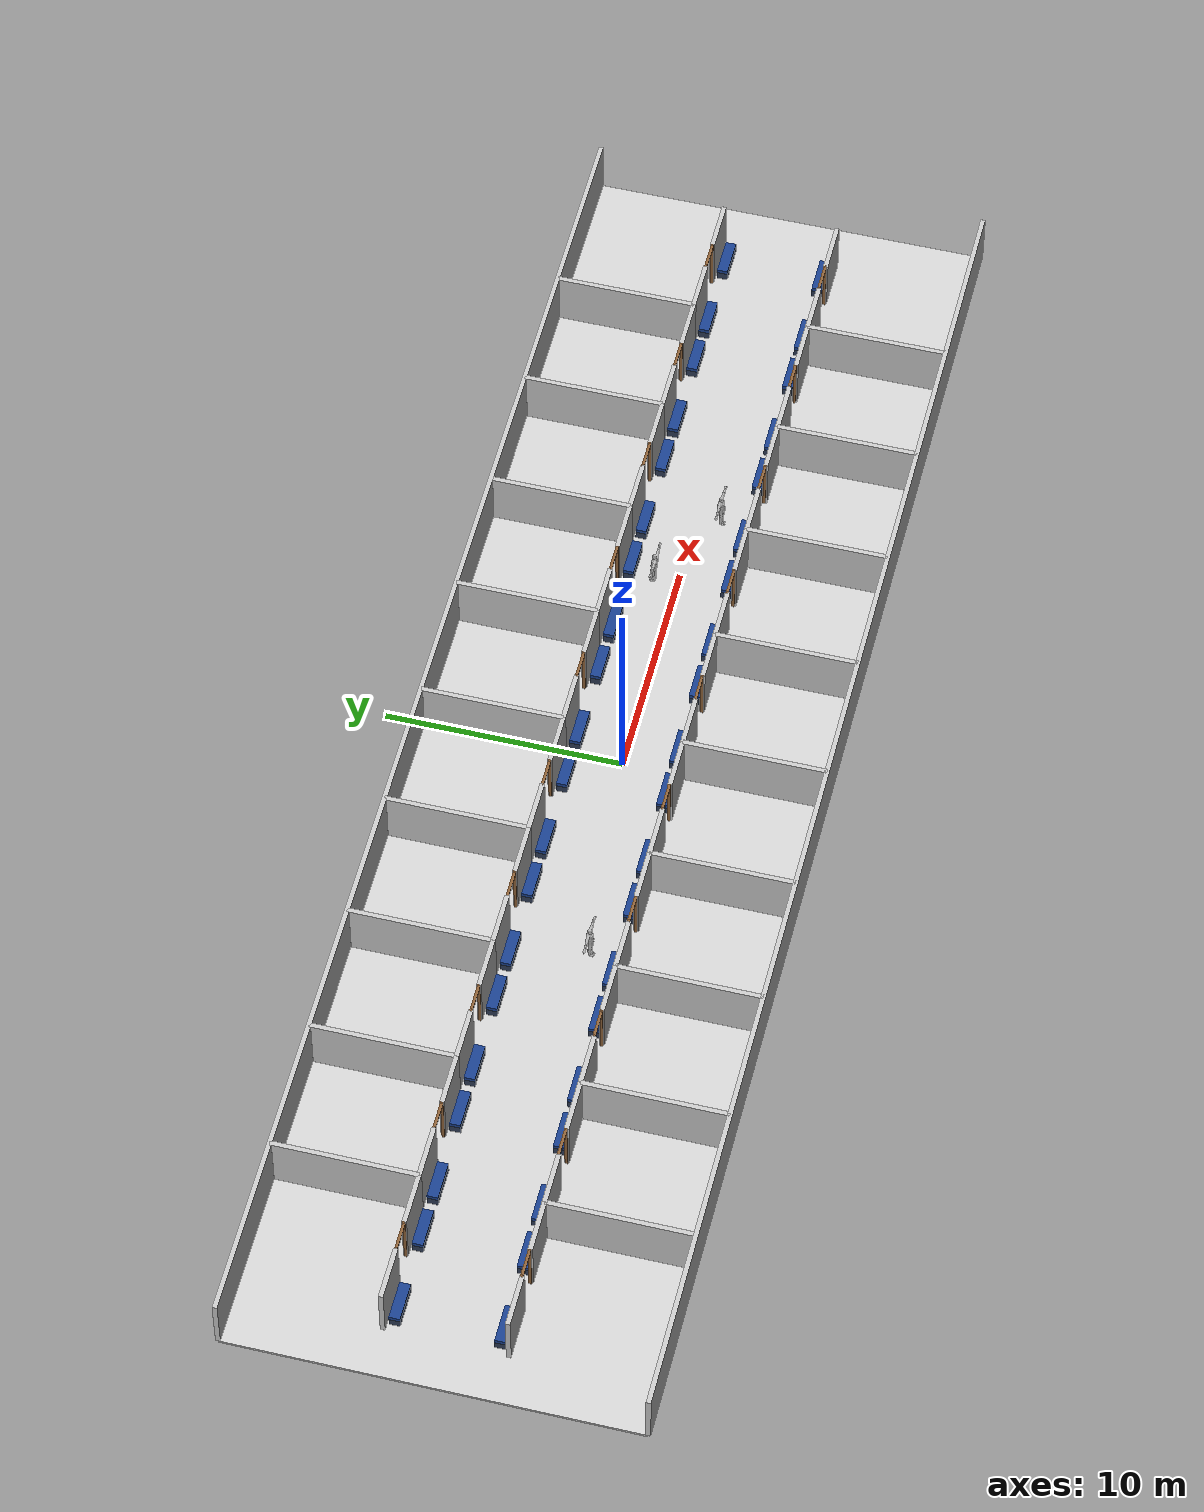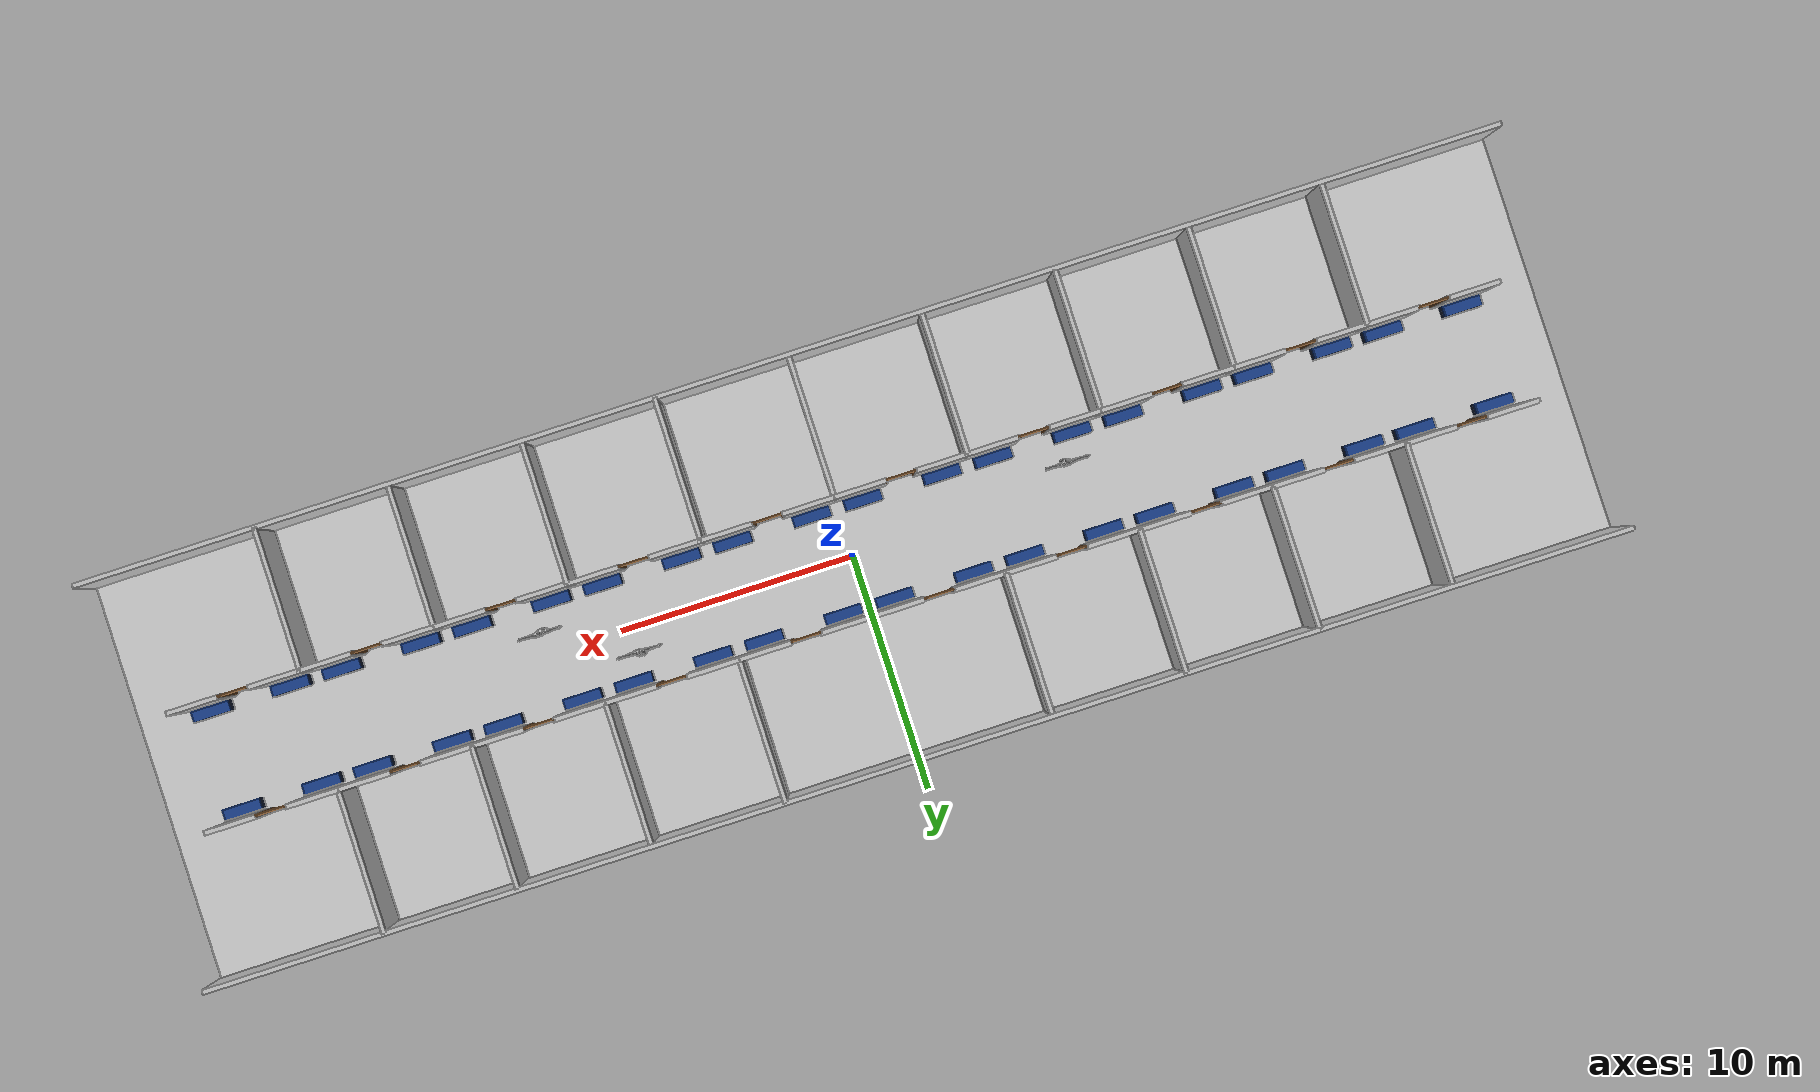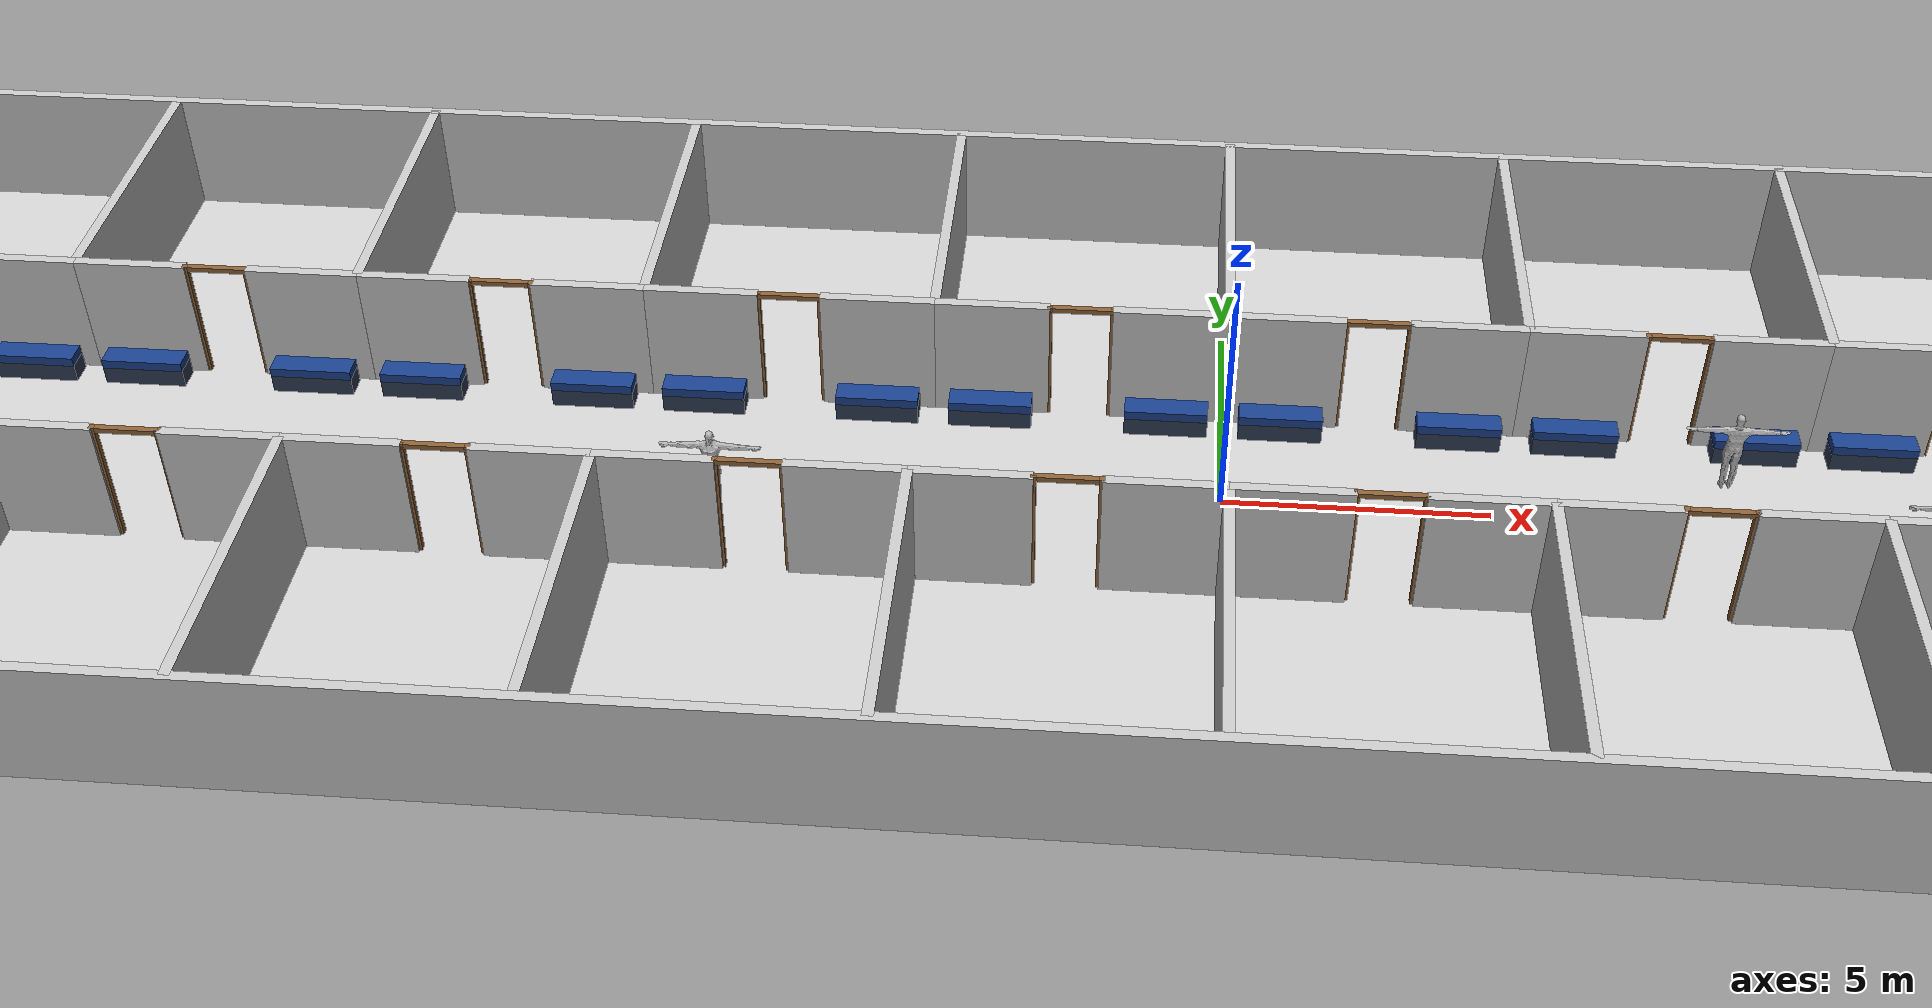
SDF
<sdf version="1.9">
 <world name="hospital_medium">
  <gravity>0 0 -9.81</gravity>
  <plugin filename="gz-sim-physics-system" name="gz::sim::systems::Physics"/>
  <plugin filename="gz-sim-user-commands-system" name="gz::sim::systems::UserCommands"/>
  <plugin filename="gz-sim-scene-broadcaster-system" name="gz::sim::systems::SceneBroadcaster"/>
  <plugin filename="gz-sim-sensors-system" name="gz::sim::systems::Sensors">
   <render_engine>ogre2</render_engine>
  </plugin>
  <plugin filename="librvo2_human_system.so" name="custom_corridor::RVO2HumanSystem">
   <human_count>8</human_count>
   <robot_name>burger</robot_name>
   <robot_radius>0.28</robot_radius>
   <human_radius>0.28</human_radius>
   <corridor_mode>false</corridor_mode>
   <politeness_balance_point>0.60</politeness_balance_point>
   <randomize_politeness>true</randomize_politeness>
   <default_scenario_file>hospital_medium</default_scenario_file>
  </plugin>
  <physics name="default_physics" type="ode">
   <max_step_size>0.004</max_step_size>
   <real_time_factor>1.0</real_time_factor>
   <real_time_update_rate>250</real_time_update_rate>
  </physics>
  <scene>
   <ambient>0.55 0.55 0.55 1</ambient>
   <background>0.75 0.75 0.75 1</background>
   <shadows>false</shadows>
  </scene>
  <light name="hospital_sun" type="directional">
   <pose>0 0 20 0 0 0</pose>
   <direction>-0.3 0.2 -1.0</direction>
   <diffuse>1 1 1 1</diffuse>
   <specular>0.3 0.3 0.3 1</specular>
   <attenuation>
    <range>1000</range>
    <constant>0.9</constant>
    <linear>0.01</linear>
    <quadratic>0.001</quadratic>
   </attenuation>
   <cast_shadows>false</cast_shadows>
  </light>
  <model name="hospital_floor">
   <static>true</static>
   <pose>0.000 0.000 -0.050 0 0 0</pose>
   <link name="link">
    <collision name="collision"><geometry><box><size>60.000 17.000 0.100</size></box></geometry></collision>
    <visual name="visual">
     <geometry><box><size>60.000 17.000 0.100</size></box></geometry>
     <material><ambient>0.82 0.82 0.82 1.0</ambient><diffuse>0.82 0.82 0.82 1.0</diffuse></material>
    </visual>
   </link>
  </model>
  <model name="north_outer_wall">
   <static>true</static>
   <pose>0.000 8.500 1.250 0 0 0</pose>
   <link name="link">
    <collision name="collision"><geometry><box><size>60.000 0.200 2.500</size></box></geometry></collision>
    <visual name="visual">
     <geometry><box><size>60.000 0.200 2.500</size></box></geometry>
     <material><ambient>0.78 0.78 0.78 1.0</ambient><diffuse>0.78 0.78 0.78 1.0</diffuse></material>
    </visual>
   </link>
  </model>
  <model name="south_outer_wall">
   <static>true</static>
   <pose>0.000 -8.500 1.250 0 0 0</pose>
   <link name="link">
    <collision name="collision"><geometry><box><size>60.000 0.200 2.500</size></box></geometry></collision>
    <visual name="visual">
     <geometry><box><size>60.000 0.200 2.500</size></box></geometry>
     <material><ambient>0.78 0.78 0.78 1.0</ambient><diffuse>0.78 0.78 0.78 1.0</diffuse></material>
    </visual>
   </link>
  </model>
  <model name="north_partition_0">
   <static>true</static>
   <pose>-22.400 5.500 1.250 0 0 0</pose>
   <link name="link">
    <collision name="collision"><geometry><box><size>0.200 6.000 2.500</size></box></geometry></collision>
    <visual name="visual">
     <geometry><box><size>0.200 6.000 2.500</size></box></geometry>
     <material><ambient>0.78 0.78 0.78 1.0</ambient><diffuse>0.78 0.78 0.78 1.0</diffuse></material>
    </visual>
   </link>
  </model>
  <model name="north_partition_1">
   <static>true</static>
   <pose>-16.800 5.500 1.250 0 0 0</pose>
   <link name="link">
    <collision name="collision"><geometry><box><size>0.200 6.000 2.500</size></box></geometry></collision>
    <visual name="visual">
     <geometry><box><size>0.200 6.000 2.500</size></box></geometry>
     <material><ambient>0.78 0.78 0.78 1.0</ambient><diffuse>0.78 0.78 0.78 1.0</diffuse></material>
    </visual>
   </link>
  </model>
  <model name="north_partition_2">
   <static>true</static>
   <pose>-11.200 5.500 1.250 0 0 0</pose>
   <link name="link">
    <collision name="collision"><geometry><box><size>0.200 6.000 2.500</size></box></geometry></collision>
    <visual name="visual">
     <geometry><box><size>0.200 6.000 2.500</size></box></geometry>
     <material><ambient>0.78 0.78 0.78 1.0</ambient><diffuse>0.78 0.78 0.78 1.0</diffuse></material>
    </visual>
   </link>
  </model>
  <model name="north_partition_3">
   <static>true</static>
   <pose>-5.600 5.500 1.250 0 0 0</pose>
   <link name="link">
    <collision name="collision"><geometry><box><size>0.200 6.000 2.500</size></box></geometry></collision>
    <visual name="visual">
     <geometry><box><size>0.200 6.000 2.500</size></box></geometry>
     <material><ambient>0.78 0.78 0.78 1.0</ambient><diffuse>0.78 0.78 0.78 1.0</diffuse></material>
    </visual>
   </link>
  </model>
  <model name="north_partition_4">
   <static>true</static>
   <pose>0.000 5.500 1.250 0 0 0</pose>
   <link name="link">
    <collision name="collision"><geometry><box><size>0.200 6.000 2.500</size></box></geometry></collision>
    <visual name="visual">
     <geometry><box><size>0.200 6.000 2.500</size></box></geometry>
     <material><ambient>0.78 0.78 0.78 1.0</ambient><diffuse>0.78 0.78 0.78 1.0</diffuse></material>
    </visual>
   </link>
  </model>
  <model name="north_partition_5">
   <static>true</static>
   <pose>5.600 5.500 1.250 0 0 0</pose>
   <link name="link">
    <collision name="collision"><geometry><box><size>0.200 6.000 2.500</size></box></geometry></collision>
    <visual name="visual">
     <geometry><box><size>0.200 6.000 2.500</size></box></geometry>
     <material><ambient>0.78 0.78 0.78 1.0</ambient><diffuse>0.78 0.78 0.78 1.0</diffuse></material>
    </visual>
   </link>
  </model>
  <model name="north_partition_6">
   <static>true</static>
   <pose>11.200 5.500 1.250 0 0 0</pose>
   <link name="link">
    <collision name="collision"><geometry><box><size>0.200 6.000 2.500</size></box></geometry></collision>
    <visual name="visual">
     <geometry><box><size>0.200 6.000 2.500</size></box></geometry>
     <material><ambient>0.78 0.78 0.78 1.0</ambient><diffuse>0.78 0.78 0.78 1.0</diffuse></material>
    </visual>
   </link>
  </model>
  <model name="north_partition_7">
   <static>true</static>
   <pose>16.800 5.500 1.250 0 0 0</pose>
   <link name="link">
    <collision name="collision"><geometry><box><size>0.200 6.000 2.500</size></box></geometry></collision>
    <visual name="visual">
     <geometry><box><size>0.200 6.000 2.500</size></box></geometry>
     <material><ambient>0.78 0.78 0.78 1.0</ambient><diffuse>0.78 0.78 0.78 1.0</diffuse></material>
    </visual>
   </link>
  </model>
  <model name="north_partition_8">
   <static>true</static>
   <pose>22.400 5.500 1.250 0 0 0</pose>
   <link name="link">
    <collision name="collision"><geometry><box><size>0.200 6.000 2.500</size></box></geometry></collision>
    <visual name="visual">
     <geometry><box><size>0.200 6.000 2.500</size></box></geometry>
     <material><ambient>0.78 0.78 0.78 1.0</ambient><diffuse>0.78 0.78 0.78 1.0</diffuse></material>
    </visual>
   </link>
  </model>
  <model name="south_partition_0">
   <static>true</static>
   <pose>-22.400 -5.500 1.250 0 0 0</pose>
   <link name="link">
    <collision name="collision"><geometry><box><size>0.200 6.000 2.500</size></box></geometry></collision>
    <visual name="visual">
     <geometry><box><size>0.200 6.000 2.500</size></box></geometry>
     <material><ambient>0.78 0.78 0.78 1.0</ambient><diffuse>0.78 0.78 0.78 1.0</diffuse></material>
    </visual>
   </link>
  </model>
  <model name="south_partition_1">
   <static>true</static>
   <pose>-16.800 -5.500 1.250 0 0 0</pose>
   <link name="link">
    <collision name="collision"><geometry><box><size>0.200 6.000 2.500</size></box></geometry></collision>
    <visual name="visual">
     <geometry><box><size>0.200 6.000 2.500</size></box></geometry>
     <material><ambient>0.78 0.78 0.78 1.0</ambient><diffuse>0.78 0.78 0.78 1.0</diffuse></material>
    </visual>
   </link>
  </model>
  <model name="south_partition_2">
   <static>true</static>
   <pose>-11.200 -5.500 1.250 0 0 0</pose>
   <link name="link">
    <collision name="collision"><geometry><box><size>0.200 6.000 2.500</size></box></geometry></collision>
    <visual name="visual">
     <geometry><box><size>0.200 6.000 2.500</size></box></geometry>
     <material><ambient>0.78 0.78 0.78 1.0</ambient><diffuse>0.78 0.78 0.78 1.0</diffuse></material>
    </visual>
   </link>
  </model>
  <model name="south_partition_3">
   <static>true</static>
   <pose>-5.600 -5.500 1.250 0 0 0</pose>
   <link name="link">
    <collision name="collision"><geometry><box><size>0.200 6.000 2.500</size></box></geometry></collision>
    <visual name="visual">
     <geometry><box><size>0.200 6.000 2.500</size></box></geometry>
     <material><ambient>0.78 0.78 0.78 1.0</ambient><diffuse>0.78 0.78 0.78 1.0</diffuse></material>
    </visual>
   </link>
  </model>
  <model name="south_partition_4">
   <static>true</static>
   <pose>0.000 -5.500 1.250 0 0 0</pose>
   <link name="link">
    <collision name="collision"><geometry><box><size>0.200 6.000 2.500</size></box></geometry></collision>
    <visual name="visual">
     <geometry><box><size>0.200 6.000 2.500</size></box></geometry>
     <material><ambient>0.78 0.78 0.78 1.0</ambient><diffuse>0.78 0.78 0.78 1.0</diffuse></material>
    </visual>
   </link>
  </model>
  <model name="south_partition_5">
   <static>true</static>
   <pose>5.600 -5.500 1.250 0 0 0</pose>
   <link name="link">
    <collision name="collision"><geometry><box><size>0.200 6.000 2.500</size></box></geometry></collision>
    <visual name="visual">
     <geometry><box><size>0.200 6.000 2.500</size></box></geometry>
     <material><ambient>0.78 0.78 0.78 1.0</ambient><diffuse>0.78 0.78 0.78 1.0</diffuse></material>
    </visual>
   </link>
  </model>
  <model name="south_partition_6">
   <static>true</static>
   <pose>11.200 -5.500 1.250 0 0 0</pose>
   <link name="link">
    <collision name="collision"><geometry><box><size>0.200 6.000 2.500</size></box></geometry></collision>
    <visual name="visual">
     <geometry><box><size>0.200 6.000 2.500</size></box></geometry>
     <material><ambient>0.78 0.78 0.78 1.0</ambient><diffuse>0.78 0.78 0.78 1.0</diffuse></material>
    </visual>
   </link>
  </model>
  <model name="south_partition_7">
   <static>true</static>
   <pose>16.800 -5.500 1.250 0 0 0</pose>
   <link name="link">
    <collision name="collision"><geometry><box><size>0.200 6.000 2.500</size></box></geometry></collision>
    <visual name="visual">
     <geometry><box><size>0.200 6.000 2.500</size></box></geometry>
     <material><ambient>0.78 0.78 0.78 1.0</ambient><diffuse>0.78 0.78 0.78 1.0</diffuse></material>
    </visual>
   </link>
  </model>
  <model name="south_partition_8">
   <static>true</static>
   <pose>22.400 -5.500 1.250 0 0 0</pose>
   <link name="link">
    <collision name="collision"><geometry><box><size>0.200 6.000 2.500</size></box></geometry></collision>
    <visual name="visual">
     <geometry><box><size>0.200 6.000 2.500</size></box></geometry>
     <material><ambient>0.78 0.78 0.78 1.0</ambient><diffuse>0.78 0.78 0.78 1.0</diffuse></material>
    </visual>
   </link>
  </model>
  <model name="north_room_01_wall_left">
   <static>true</static>
   <pose>-26.900 2.500 1.250 0 0 0</pose>
   <link name="link">
    <collision name="collision"><geometry><box><size>2.200 0.200 2.500</size></box></geometry></collision>
    <visual name="visual">
     <geometry><box><size>2.200 0.200 2.500</size></box></geometry>
     <material><ambient>0.78 0.78 0.78 1.0</ambient><diffuse>0.78 0.78 0.78 1.0</diffuse></material>
    </visual>
   </link>
  </model>
  <model name="north_room_01_wall_right">
   <static>true</static>
   <pose>-23.500 2.500 1.250 0 0 0</pose>
   <link name="link">
    <collision name="collision"><geometry><box><size>2.200 0.200 2.500</size></box></geometry></collision>
    <visual name="visual">
     <geometry><box><size>2.200 0.200 2.500</size></box></geometry>
     <material><ambient>0.78 0.78 0.78 1.0</ambient><diffuse>0.78 0.78 0.78 1.0</diffuse></material>
    </visual>
   </link>
  </model>
  <model name="north_room_02_wall_left">
   <static>true</static>
   <pose>-21.300 2.500 1.250 0 0 0</pose>
   <link name="link">
    <collision name="collision"><geometry><box><size>2.200 0.200 2.500</size></box></geometry></collision>
    <visual name="visual">
     <geometry><box><size>2.200 0.200 2.500</size></box></geometry>
     <material><ambient>0.78 0.78 0.78 1.0</ambient><diffuse>0.78 0.78 0.78 1.0</diffuse></material>
    </visual>
   </link>
  </model>
  <model name="north_room_02_wall_right">
   <static>true</static>
   <pose>-17.900 2.500 1.250 0 0 0</pose>
   <link name="link">
    <collision name="collision"><geometry><box><size>2.200 0.200 2.500</size></box></geometry></collision>
    <visual name="visual">
     <geometry><box><size>2.200 0.200 2.500</size></box></geometry>
     <material><ambient>0.78 0.78 0.78 1.0</ambient><diffuse>0.78 0.78 0.78 1.0</diffuse></material>
    </visual>
   </link>
  </model>
  <model name="north_room_03_wall_left">
   <static>true</static>
   <pose>-15.700 2.500 1.250 0 0 0</pose>
   <link name="link">
    <collision name="collision"><geometry><box><size>2.200 0.200 2.500</size></box></geometry></collision>
    <visual name="visual">
     <geometry><box><size>2.200 0.200 2.500</size></box></geometry>
     <material><ambient>0.78 0.78 0.78 1.0</ambient><diffuse>0.78 0.78 0.78 1.0</diffuse></material>
    </visual>
   </link>
  </model>
  <model name="north_room_03_wall_right">
   <static>true</static>
   <pose>-12.300 2.500 1.250 0 0 0</pose>
   <link name="link">
    <collision name="collision"><geometry><box><size>2.200 0.200 2.500</size></box></geometry></collision>
    <visual name="visual">
     <geometry><box><size>2.200 0.200 2.500</size></box></geometry>
     <material><ambient>0.78 0.78 0.78 1.0</ambient><diffuse>0.78 0.78 0.78 1.0</diffuse></material>
    </visual>
   </link>
  </model>
  <model name="north_room_04_wall_left">
   <static>true</static>
   <pose>-10.100 2.500 1.250 0 0 0</pose>
   <link name="link">
    <collision name="collision"><geometry><box><size>2.200 0.200 2.500</size></box></geometry></collision>
    <visual name="visual">
     <geometry><box><size>2.200 0.200 2.500</size></box></geometry>
     <material><ambient>0.78 0.78 0.78 1.0</ambient><diffuse>0.78 0.78 0.78 1.0</diffuse></material>
    </visual>
   </link>
  </model>
  <model name="north_room_04_wall_right">
   <static>true</static>
   <pose>-6.700 2.500 1.250 0 0 0</pose>
   <link name="link">
    <collision name="collision"><geometry><box><size>2.200 0.200 2.500</size></box></geometry></collision>
    <visual name="visual">
     <geometry><box><size>2.200 0.200 2.500</size></box></geometry>
     <material><ambient>0.78 0.78 0.78 1.0</ambient><diffuse>0.78 0.78 0.78 1.0</diffuse></material>
    </visual>
   </link>
  </model>
  <model name="north_room_05_wall_left">
   <static>true</static>
   <pose>-4.500 2.500 1.250 0 0 0</pose>
   <link name="link">
    <collision name="collision"><geometry><box><size>2.200 0.200 2.500</size></box></geometry></collision>
    <visual name="visual">
     <geometry><box><size>2.200 0.200 2.500</size></box></geometry>
     <material><ambient>0.78 0.78 0.78 1.0</ambient><diffuse>0.78 0.78 0.78 1.0</diffuse></material>
    </visual>
   </link>
  </model>
  <model name="north_room_05_wall_right">
   <static>true</static>
   <pose>-1.100 2.500 1.250 0 0 0</pose>
   <link name="link">
    <collision name="collision"><geometry><box><size>2.200 0.200 2.500</size></box></geometry></collision>
    <visual name="visual">
     <geometry><box><size>2.200 0.200 2.500</size></box></geometry>
     <material><ambient>0.78 0.78 0.78 1.0</ambient><diffuse>0.78 0.78 0.78 1.0</diffuse></material>
    </visual>
   </link>
  </model>
  <model name="north_room_06_wall_left">
   <static>true</static>
   <pose>1.100 2.500 1.250 0 0 0</pose>
   <link name="link">
    <collision name="collision"><geometry><box><size>2.200 0.200 2.500</size></box></geometry></collision>
    <visual name="visual">
     <geometry><box><size>2.200 0.200 2.500</size></box></geometry>
     <material><ambient>0.78 0.78 0.78 1.0</ambient><diffuse>0.78 0.78 0.78 1.0</diffuse></material>
    </visual>
   </link>
  </model>
  <model name="north_room_06_wall_right">
   <static>true</static>
   <pose>4.500 2.500 1.250 0 0 0</pose>
   <link name="link">
    <collision name="collision"><geometry><box><size>2.200 0.200 2.500</size></box></geometry></collision>
    <visual name="visual">
     <geometry><box><size>2.200 0.200 2.500</size></box></geometry>
     <material><ambient>0.78 0.78 0.78 1.0</ambient><diffuse>0.78 0.78 0.78 1.0</diffuse></material>
    </visual>
   </link>
  </model>
  <model name="north_room_07_wall_left">
   <static>true</static>
   <pose>6.700 2.500 1.250 0 0 0</pose>
   <link name="link">
    <collision name="collision"><geometry><box><size>2.200 0.200 2.500</size></box></geometry></collision>
    <visual name="visual">
     <geometry><box><size>2.200 0.200 2.500</size></box></geometry>
     <material><ambient>0.78 0.78 0.78 1.0</ambient><diffuse>0.78 0.78 0.78 1.0</diffuse></material>
    </visual>
   </link>
  </model>
  <model name="north_room_07_wall_right">
   <static>true</static>
   <pose>10.100 2.500 1.250 0 0 0</pose>
   <link name="link">
    <collision name="collision"><geometry><box><size>2.200 0.200 2.500</size></box></geometry></collision>
    <visual name="visual">
     <geometry><box><size>2.200 0.200 2.500</size></box></geometry>
     <material><ambient>0.78 0.78 0.78 1.0</ambient><diffuse>0.78 0.78 0.78 1.0</diffuse></material>
    </visual>
   </link>
  </model>
  <model name="north_room_08_wall_left">
   <static>true</static>
   <pose>12.300 2.500 1.250 0 0 0</pose>
   <link name="link">
    <collision name="collision"><geometry><box><size>2.200 0.200 2.500</size></box></geometry></collision>
    <visual name="visual">
     <geometry><box><size>2.200 0.200 2.500</size></box></geometry>
     <material><ambient>0.78 0.78 0.78 1.0</ambient><diffuse>0.78 0.78 0.78 1.0</diffuse></material>
    </visual>
   </link>
  </model>
  <model name="north_room_08_wall_right">
   <static>true</static>
   <pose>15.700 2.500 1.250 0 0 0</pose>
   <link name="link">
    <collision name="collision"><geometry><box><size>2.200 0.200 2.500</size></box></geometry></collision>
    <visual name="visual">
     <geometry><box><size>2.200 0.200 2.500</size></box></geometry>
     <material><ambient>0.78 0.78 0.78 1.0</ambient><diffuse>0.78 0.78 0.78 1.0</diffuse></material>
    </visual>
   </link>
  </model>
  <model name="north_room_09_wall_left">
   <static>true</static>
   <pose>17.900 2.500 1.250 0 0 0</pose>
   <link name="link">
    <collision name="collision"><geometry><box><size>2.200 0.200 2.500</size></box></geometry></collision>
    <visual name="visual">
     <geometry><box><size>2.200 0.200 2.500</size></box></geometry>
     <material><ambient>0.78 0.78 0.78 1.0</ambient><diffuse>0.78 0.78 0.78 1.0</diffuse></material>
    </visual>
   </link>
  </model>
  <model name="north_room_09_wall_right">
   <static>true</static>
   <pose>21.300 2.500 1.250 0 0 0</pose>
   <link name="link">
    <collision name="collision"><geometry><box><size>2.200 0.200 2.500</size></box></geometry></collision>
    <visual name="visual">
     <geometry><box><size>2.200 0.200 2.500</size></box></geometry>
     <material><ambient>0.78 0.78 0.78 1.0</ambient><diffuse>0.78 0.78 0.78 1.0</diffuse></material>
    </visual>
   </link>
  </model>
  <model name="north_room_10_wall_left">
   <static>true</static>
   <pose>23.500 2.500 1.250 0 0 0</pose>
   <link name="link">
    <collision name="collision"><geometry><box><size>2.200 0.200 2.500</size></box></geometry></collision>
    <visual name="visual">
     <geometry><box><size>2.200 0.200 2.500</size></box></geometry>
     <material><ambient>0.78 0.78 0.78 1.0</ambient><diffuse>0.78 0.78 0.78 1.0</diffuse></material>
    </visual>
   </link>
  </model>
  <model name="north_room_10_wall_right">
   <static>true</static>
   <pose>26.900 2.500 1.250 0 0 0</pose>
   <link name="link">
    <collision name="collision"><geometry><box><size>2.200 0.200 2.500</size></box></geometry></collision>
    <visual name="visual">
     <geometry><box><size>2.200 0.200 2.500</size></box></geometry>
     <material><ambient>0.78 0.78 0.78 1.0</ambient><diffuse>0.78 0.78 0.78 1.0</diffuse></material>
    </visual>
   </link>
  </model>
  <model name="south_room_01_wall_left">
   <static>true</static>
   <pose>-26.900 -2.500 1.250 0 0 0</pose>
   <link name="link">
    <collision name="collision"><geometry><box><size>2.200 0.200 2.500</size></box></geometry></collision>
    <visual name="visual">
     <geometry><box><size>2.200 0.200 2.500</size></box></geometry>
     <material><ambient>0.78 0.78 0.78 1.0</ambient><diffuse>0.78 0.78 0.78 1.0</diffuse></material>
    </visual>
   </link>
  </model>
  <model name="south_room_01_wall_right">
   <static>true</static>
   <pose>-23.500 -2.500 1.250 0 0 0</pose>
   <link name="link">
    <collision name="collision"><geometry><box><size>2.200 0.200 2.500</size></box></geometry></collision>
    <visual name="visual">
     <geometry><box><size>2.200 0.200 2.500</size></box></geometry>
     <material><ambient>0.78 0.78 0.78 1.0</ambient><diffuse>0.78 0.78 0.78 1.0</diffuse></material>
    </visual>
   </link>
  </model>
  <model name="south_room_02_wall_left">
   <static>true</static>
   <pose>-21.300 -2.500 1.250 0 0 0</pose>
   <link name="link">
    <collision name="collision"><geometry><box><size>2.200 0.200 2.500</size></box></geometry></collision>
    <visual name="visual">
     <geometry><box><size>2.200 0.200 2.500</size></box></geometry>
     <material><ambient>0.78 0.78 0.78 1.0</ambient><diffuse>0.78 0.78 0.78 1.0</diffuse></material>
    </visual>
   </link>
  </model>
  <model name="south_room_02_wall_right">
   <static>true</static>
   <pose>-17.900 -2.500 1.250 0 0 0</pose>
   <link name="link">
    <collision name="collision"><geometry><box><size>2.200 0.200 2.500</size></box></geometry></collision>
    <visual name="visual">
     <geometry><box><size>2.200 0.200 2.500</size></box></geometry>
     <material><ambient>0.78 0.78 0.78 1.0</ambient><diffuse>0.78 0.78 0.78 1.0</diffuse></material>
    </visual>
   </link>
  </model>
  <model name="south_room_03_wall_left">
   <static>true</static>
   <pose>-15.700 -2.500 1.250 0 0 0</pose>
   <link name="link">
    <collision name="collision"><geometry><box><size>2.200 0.200 2.500</size></box></geometry></collision>
    <visual name="visual">
     <geometry><box><size>2.200 0.200 2.500</size></box></geometry>
     <material><ambient>0.78 0.78 0.78 1.0</ambient><diffuse>0.78 0.78 0.78 1.0</diffuse></material>
    </visual>
   </link>
  </model>
  <model name="south_room_03_wall_right">
   <static>true</static>
   <pose>-12.300 -2.500 1.250 0 0 0</pose>
   <link name="link">
    <collision name="collision"><geometry><box><size>2.200 0.200 2.500</size></box></geometry></collision>
    <visual name="visual">
     <geometry><box><size>2.200 0.200 2.500</size></box></geometry>
     <material><ambient>0.78 0.78 0.78 1.0</ambient><diffuse>0.78 0.78 0.78 1.0</diffuse></material>
    </visual>
   </link>
  </model>
  <model name="south_room_04_wall_left">
   <static>true</static>
   <pose>-10.100 -2.500 1.250 0 0 0</pose>
   <link name="link">
    <collision name="collision"><geometry><box><size>2.200 0.200 2.500</size></box></geometry></collision>
    <visual name="visual">
     <geometry><box><size>2.200 0.200 2.500</size></box></geometry>
     <material><ambient>0.78 0.78 0.78 1.0</ambient><diffuse>0.78 0.78 0.78 1.0</diffuse></material>
    </visual>
   </link>
  </model>
  <model name="south_room_04_wall_right">
   <static>true</static>
   <pose>-6.700 -2.500 1.250 0 0 0</pose>
   <link name="link">
    <collision name="collision"><geometry><box><size>2.200 0.200 2.500</size></box></geometry></collision>
    <visual name="visual">
     <geometry><box><size>2.200 0.200 2.500</size></box></geometry>
     <material><ambient>0.78 0.78 0.78 1.0</ambient><diffuse>0.78 0.78 0.78 1.0</diffuse></material>
    </visual>
   </link>
  </model>
  <model name="south_room_05_wall_left">
   <static>true</static>
   <pose>-4.500 -2.500 1.250 0 0 0</pose>
   <link name="link">
    <collision name="collision"><geometry><box><size>2.200 0.200 2.500</size></box></geometry></collision>
    <visual name="visual">
     <geometry><box><size>2.200 0.200 2.500</size></box></geometry>
     <material><ambient>0.78 0.78 0.78 1.0</ambient><diffuse>0.78 0.78 0.78 1.0</diffuse></material>
    </visual>
   </link>
  </model>
  <model name="south_room_05_wall_right">
   <static>true</static>
   <pose>-1.100 -2.500 1.250 0 0 0</pose>
   <link name="link">
    <collision name="collision"><geometry><box><size>2.200 0.200 2.500</size></box></geometry></collision>
    <visual name="visual">
     <geometry><box><size>2.200 0.200 2.500</size></box></geometry>
     <material><ambient>0.78 0.78 0.78 1.0</ambient><diffuse>0.78 0.78 0.78 1.0</diffuse></material>
    </visual>
   </link>
  </model>
  <model name="south_room_06_wall_left">
   <static>true</static>
   <pose>1.100 -2.500 1.250 0 0 0</pose>
   <link name="link">
    <collision name="collision"><geometry><box><size>2.200 0.200 2.500</size></box></geometry></collision>
    <visual name="visual">
     <geometry><box><size>2.200 0.200 2.500</size></box></geometry>
     <material><ambient>0.78 0.78 0.78 1.0</ambient><diffuse>0.78 0.78 0.78 1.0</diffuse></material>
    </visual>
   </link>
  </model>
  <model name="south_room_06_wall_right">
   <static>true</static>
   <pose>4.500 -2.500 1.250 0 0 0</pose>
   <link name="link">
    <collision name="collision"><geometry><box><size>2.200 0.200 2.500</size></box></geometry></collision>
    <visual name="visual">
     <geometry><box><size>2.200 0.200 2.500</size></box></geometry>
     <material><ambient>0.78 0.78 0.78 1.0</ambient><diffuse>0.78 0.78 0.78 1.0</diffuse></material>
    </visual>
   </link>
  </model>
  <model name="south_room_07_wall_left">
   <static>true</static>
   <pose>6.700 -2.500 1.250 0 0 0</pose>
   <link name="link">
    <collision name="collision"><geometry><box><size>2.200 0.200 2.500</size></box></geometry></collision>
    <visual name="visual">
     <geometry><box><size>2.200 0.200 2.500</size></box></geometry>
     <material><ambient>0.78 0.78 0.78 1.0</ambient><diffuse>0.78 0.78 0.78 1.0</diffuse></material>
    </visual>
   </link>
  </model>
  <model name="south_room_07_wall_right">
   <static>true</static>
   <pose>10.100 -2.500 1.250 0 0 0</pose>
   <link name="link">
    <collision name="collision"><geometry><box><size>2.200 0.200 2.500</size></box></geometry></collision>
    <visual name="visual">
     <geometry><box><size>2.200 0.200 2.500</size></box></geometry>
     <material><ambient>0.78 0.78 0.78 1.0</ambient><diffuse>0.78 0.78 0.78 1.0</diffuse></material>
    </visual>
   </link>
  </model>
  <model name="south_room_08_wall_left">
   <static>true</static>
   <pose>12.300 -2.500 1.250 0 0 0</pose>
   <link name="link">
    <collision name="collision"><geometry><box><size>2.200 0.200 2.500</size></box></geometry></collision>
    <visual name="visual">
     <geometry><box><size>2.200 0.200 2.500</size></box></geometry>
     <material><ambient>0.78 0.78 0.78 1.0</ambient><diffuse>0.78 0.78 0.78 1.0</diffuse></material>
    </visual>
   </link>
  </model>
  <model name="south_room_08_wall_right">
   <static>true</static>
   <pose>15.700 -2.500 1.250 0 0 0</pose>
   <link name="link">
    <collision name="collision"><geometry><box><size>2.200 0.200 2.500</size></box></geometry></collision>
    <visual name="visual">
     <geometry><box><size>2.200 0.200 2.500</size></box></geometry>
     <material><ambient>0.78 0.78 0.78 1.0</ambient><diffuse>0.78 0.78 0.78 1.0</diffuse></material>
    </visual>
   </link>
  </model>
  <model name="south_room_09_wall_left">
   <static>true</static>
   <pose>17.900 -2.500 1.250 0 0 0</pose>
   <link name="link">
    <collision name="collision"><geometry><box><size>2.200 0.200 2.500</size></box></geometry></collision>
    <visual name="visual">
     <geometry><box><size>2.200 0.200 2.500</size></box></geometry>
     <material><ambient>0.78 0.78 0.78 1.0</ambient><diffuse>0.78 0.78 0.78 1.0</diffuse></material>
    </visual>
   </link>
  </model>
  <model name="south_room_09_wall_right">
   <static>true</static>
   <pose>21.300 -2.500 1.250 0 0 0</pose>
   <link name="link">
    <collision name="collision"><geometry><box><size>2.200 0.200 2.500</size></box></geometry></collision>
    <visual name="visual">
     <geometry><box><size>2.200 0.200 2.500</size></box></geometry>
     <material><ambient>0.78 0.78 0.78 1.0</ambient><diffuse>0.78 0.78 0.78 1.0</diffuse></material>
    </visual>
   </link>
  </model>
  <model name="south_room_10_wall_left">
   <static>true</static>
   <pose>23.500 -2.500 1.250 0 0 0</pose>
   <link name="link">
    <collision name="collision"><geometry><box><size>2.200 0.200 2.500</size></box></geometry></collision>
    <visual name="visual">
     <geometry><box><size>2.200 0.200 2.500</size></box></geometry>
     <material><ambient>0.78 0.78 0.78 1.0</ambient><diffuse>0.78 0.78 0.78 1.0</diffuse></material>
    </visual>
   </link>
  </model>
  <model name="south_room_10_wall_right">
   <static>true</static>
   <pose>26.900 -2.500 1.250 0 0 0</pose>
   <link name="link">
    <collision name="collision"><geometry><box><size>2.200 0.200 2.500</size></box></geometry></collision>
    <visual name="visual">
     <geometry><box><size>2.200 0.200 2.500</size></box></geometry>
     <material><ambient>0.78 0.78 0.78 1.0</ambient><diffuse>0.78 0.78 0.78 1.0</diffuse></material>
    </visual>
   </link>
  </model>
  <model name="north_door_01_left">
   <static>true</static>
   <pose>-25.800 2.490 1.250 0 0 0</pose>
   <link name="link">
    <collision name="collision"><geometry><box><size>0.100 0.120 2.500</size></box></geometry></collision>
    <visual name="visual">
     <geometry><box><size>0.100 0.120 2.500</size></box></geometry>
     <material><ambient>0.55 0.38 0.22 1.0</ambient><diffuse>0.55 0.38 0.22 1.0</diffuse></material>
    </visual>
   </link>
  </model>
  <model name="north_door_01_right">
   <static>true</static>
   <pose>-24.600 2.490 1.250 0 0 0</pose>
   <link name="link">
    <collision name="collision"><geometry><box><size>0.100 0.120 2.500</size></box></geometry></collision>
    <visual name="visual">
     <geometry><box><size>0.100 0.120 2.500</size></box></geometry>
     <material><ambient>0.55 0.38 0.22 1.0</ambient><diffuse>0.55 0.38 0.22 1.0</diffuse></material>
    </visual>
   </link>
  </model>
  <model name="north_door_01_top">
   <static>true</static>
   <pose>-25.200 2.490 2.450 0 0 0</pose>
   <link name="link">
    <collision name="collision"><geometry><box><size>1.200 0.120 0.100</size></box></geometry></collision>
    <visual name="visual">
     <geometry><box><size>1.200 0.120 0.100</size></box></geometry>
     <material><ambient>0.55 0.38 0.22 1.0</ambient><diffuse>0.55 0.38 0.22 1.0</diffuse></material>
    </visual>
   </link>
  </model>
  <model name="north_door_02_left">
   <static>true</static>
   <pose>-20.200 2.490 1.250 0 0 0</pose>
   <link name="link">
    <collision name="collision"><geometry><box><size>0.100 0.120 2.500</size></box></geometry></collision>
    <visual name="visual">
     <geometry><box><size>0.100 0.120 2.500</size></box></geometry>
     <material><ambient>0.55 0.38 0.22 1.0</ambient><diffuse>0.55 0.38 0.22 1.0</diffuse></material>
    </visual>
   </link>
  </model>
  <model name="north_door_02_right">
   <static>true</static>
   <pose>-19.000 2.490 1.250 0 0 0</pose>
   <link name="link">
    <collision name="collision"><geometry><box><size>0.100 0.120 2.500</size></box></geometry></collision>
    <visual name="visual">
     <geometry><box><size>0.100 0.120 2.500</size></box></geometry>
     <material><ambient>0.55 0.38 0.22 1.0</ambient><diffuse>0.55 0.38 0.22 1.0</diffuse></material>
    </visual>
   </link>
  </model>
  <model name="north_door_02_top">
   <static>true</static>
   <pose>-19.600 2.490 2.450 0 0 0</pose>
   <link name="link">
    <collision name="collision"><geometry><box><size>1.200 0.120 0.100</size></box></geometry></collision>
    <visual name="visual">
     <geometry><box><size>1.200 0.120 0.100</size></box></geometry>
     <material><ambient>0.55 0.38 0.22 1.0</ambient><diffuse>0.55 0.38 0.22 1.0</diffuse></material>
    </visual>
   </link>
  </model>
  <model name="north_door_03_left">
   <static>true</static>
   <pose>-14.600 2.490 1.250 0 0 0</pose>
   <link name="link">
    <collision name="collision"><geometry><box><size>0.100 0.120 2.500</size></box></geometry></collision>
    <visual name="visual">
     <geometry><box><size>0.100 0.120 2.500</size></box></geometry>
     <material><ambient>0.55 0.38 0.22 1.0</ambient><diffuse>0.55 0.38 0.22 1.0</diffuse></material>
    </visual>
   </link>
  </model>
  <model name="north_door_03_right">
   <static>true</static>
   <pose>-13.400 2.490 1.250 0 0 0</pose>
   <link name="link">
    <collision name="collision"><geometry><box><size>0.100 0.120 2.500</size></box></geometry></collision>
    <visual name="visual">
     <geometry><box><size>0.100 0.120 2.500</size></box></geometry>
     <material><ambient>0.55 0.38 0.22 1.0</ambient><diffuse>0.55 0.38 0.22 1.0</diffuse></material>
    </visual>
   </link>
  </model>
  <model name="north_door_03_top">
   <static>true</static>
   <pose>-14.000 2.490 2.450 0 0 0</pose>
   <link name="link">
    <collision name="collision"><geometry><box><size>1.200 0.120 0.100</size></box></geometry></collision>
    <visual name="visual">
     <geometry><box><size>1.200 0.120 0.100</size></box></geometry>
     <material><ambient>0.55 0.38 0.22 1.0</ambient><diffuse>0.55 0.38 0.22 1.0</diffuse></material>
    </visual>
   </link>
  </model>
  <model name="north_door_04_left">
   <static>true</static>
   <pose>-9.000 2.490 1.250 0 0 0</pose>
   <link name="link">
    <collision name="collision"><geometry><box><size>0.100 0.120 2.500</size></box></geometry></collision>
    <visual name="visual">
     <geometry><box><size>0.100 0.120 2.500</size></box></geometry>
     <material><ambient>0.55 0.38 0.22 1.0</ambient><diffuse>0.55 0.38 0.22 1.0</diffuse></material>
    </visual>
   </link>
  </model>
  <model name="north_door_04_right">
   <static>true</static>
   <pose>-7.800 2.490 1.250 0 0 0</pose>
   <link name="link">
    <collision name="collision"><geometry><box><size>0.100 0.120 2.500</size></box></geometry></collision>
    <visual name="visual">
     <geometry><box><size>0.100 0.120 2.500</size></box></geometry>
     <material><ambient>0.55 0.38 0.22 1.0</ambient><diffuse>0.55 0.38 0.22 1.0</diffuse></material>
    </visual>
   </link>
  </model>
  <model name="north_door_04_top">
   <static>true</static>
   <pose>-8.400 2.490 2.450 0 0 0</pose>
   <link name="link">
    <collision name="collision"><geometry><box><size>1.200 0.120 0.100</size></box></geometry></collision>
    <visual name="visual">
     <geometry><box><size>1.200 0.120 0.100</size></box></geometry>
     <material><ambient>0.55 0.38 0.22 1.0</ambient><diffuse>0.55 0.38 0.22 1.0</diffuse></material>
    </visual>
   </link>
  </model>
  <model name="north_door_05_left">
   <static>true</static>
   <pose>-3.400 2.490 1.250 0 0 0</pose>
   <link name="link">
    <collision name="collision"><geometry><box><size>0.100 0.120 2.500</size></box></geometry></collision>
    <visual name="visual">
     <geometry><box><size>0.100 0.120 2.500</size></box></geometry>
     <material><ambient>0.55 0.38 0.22 1.0</ambient><diffuse>0.55 0.38 0.22 1.0</diffuse></material>
    </visual>
   </link>
  </model>
  <model name="north_door_05_right">
   <static>true</static>
   <pose>-2.200 2.490 1.250 0 0 0</pose>
   <link name="link">
    <collision name="collision"><geometry><box><size>0.100 0.120 2.500</size></box></geometry></collision>
    <visual name="visual">
     <geometry><box><size>0.100 0.120 2.500</size></box></geometry>
     <material><ambient>0.55 0.38 0.22 1.0</ambient><diffuse>0.55 0.38 0.22 1.0</diffuse></material>
    </visual>
   </link>
  </model>
  <model name="north_door_05_top">
   <static>true</static>
   <pose>-2.800 2.490 2.450 0 0 0</pose>
   <link name="link">
    <collision name="collision"><geometry><box><size>1.200 0.120 0.100</size></box></geometry></collision>
    <visual name="visual">
     <geometry><box><size>1.200 0.120 0.100</size></box></geometry>
     <material><ambient>0.55 0.38 0.22 1.0</ambient><diffuse>0.55 0.38 0.22 1.0</diffuse></material>
    </visual>
   </link>
  </model>
  <model name="north_door_06_left">
   <static>true</static>
   <pose>2.200 2.490 1.250 0 0 0</pose>
   <link name="link">
    <collision name="collision"><geometry><box><size>0.100 0.120 2.500</size></box></geometry></collision>
    <visual name="visual">
     <geometry><box><size>0.100 0.120 2.500</size></box></geometry>
     <material><ambient>0.55 0.38 0.22 1.0</ambient><diffuse>0.55 0.38 0.22 1.0</diffuse></material>
    </visual>
   </link>
  </model>
  <model name="north_door_06_right">
   <static>true</static>
   <pose>3.400 2.490 1.250 0 0 0</pose>
   <link name="link">
    <collision name="collision"><geometry><box><size>0.100 0.120 2.500</size></box></geometry></collision>
    <visual name="visual">
     <geometry><box><size>0.100 0.120 2.500</size></box></geometry>
     <material><ambient>0.55 0.38 0.22 1.0</ambient><diffuse>0.55 0.38 0.22 1.0</diffuse></material>
    </visual>
   </link>
  </model>
  <model name="north_door_06_top">
   <static>true</static>
   <pose>2.800 2.490 2.450 0 0 0</pose>
   <link name="link">
    <collision name="collision"><geometry><box><size>1.200 0.120 0.100</size></box></geometry></collision>
    <visual name="visual">
     <geometry><box><size>1.200 0.120 0.100</size></box></geometry>
     <material><ambient>0.55 0.38 0.22 1.0</ambient><diffuse>0.55 0.38 0.22 1.0</diffuse></material>
    </visual>
   </link>
  </model>
  <model name="north_door_07_left">
   <static>true</static>
   <pose>7.800 2.490 1.250 0 0 0</pose>
   <link name="link">
    <collision name="collision"><geometry><box><size>0.100 0.120 2.500</size></box></geometry></collision>
    <visual name="visual">
     <geometry><box><size>0.100 0.120 2.500</size></box></geometry>
     <material><ambient>0.55 0.38 0.22 1.0</ambient><diffuse>0.55 0.38 0.22 1.0</diffuse></material>
    </visual>
   </link>
  </model>
  <model name="north_door_07_right">
   <static>true</static>
   <pose>9.000 2.490 1.250 0 0 0</pose>
   <link name="link">
    <collision name="collision"><geometry><box><size>0.100 0.120 2.500</size></box></geometry></collision>
    <visual name="visual">
     <geometry><box><size>0.100 0.120 2.500</size></box></geometry>
     <material><ambient>0.55 0.38 0.22 1.0</ambient><diffuse>0.55 0.38 0.22 1.0</diffuse></material>
    </visual>
   </link>
  </model>
  <model name="north_door_07_top">
   <static>true</static>
   <pose>8.400 2.490 2.450 0 0 0</pose>
   <link name="link">
    <collision name="collision"><geometry><box><size>1.200 0.120 0.100</size></box></geometry></collision>
    <visual name="visual">
     <geometry><box><size>1.200 0.120 0.100</size></box></geometry>
     <material><ambient>0.55 0.38 0.22 1.0</ambient><diffuse>0.55 0.38 0.22 1.0</diffuse></material>
    </visual>
   </link>
  </model>
  <model name="north_door_08_left">
   <static>true</static>
   <pose>13.400 2.490 1.250 0 0 0</pose>
   <link name="link">
    <collision name="collision"><geometry><box><size>0.100 0.120 2.500</size></box></geometry></collision>
    <visual name="visual">
     <geometry><box><size>0.100 0.120 2.500</size></box></geometry>
     <material><ambient>0.55 0.38 0.22 1.0</ambient><diffuse>0.55 0.38 0.22 1.0</diffuse></material>
    </visual>
   </link>
  </model>
  <model name="north_door_08_right">
   <static>true</static>
   <pose>14.600 2.490 1.250 0 0 0</pose>
   <link name="link">
    <collision name="collision"><geometry><box><size>0.100 0.120 2.500</size></box></geometry></collision>
    <visual name="visual">
     <geometry><box><size>0.100 0.120 2.500</size></box></geometry>
     <material><ambient>0.55 0.38 0.22 1.0</ambient><diffuse>0.55 0.38 0.22 1.0</diffuse></material>
    </visual>
   </link>
  </model>
  <model name="north_door_08_top">
   <static>true</static>
   <pose>14.000 2.490 2.450 0 0 0</pose>
   <link name="link">
    <collision name="collision"><geometry><box><size>1.200 0.120 0.100</size></box></geometry></collision>
    <visual name="visual">
     <geometry><box><size>1.200 0.120 0.100</size></box></geometry>
     <material><ambient>0.55 0.38 0.22 1.0</ambient><diffuse>0.55 0.38 0.22 1.0</diffuse></material>
    </visual>
   </link>
  </model>
  <model name="north_door_09_left">
   <static>true</static>
   <pose>19.000 2.490 1.250 0 0 0</pose>
   <link name="link">
    <collision name="collision"><geometry><box><size>0.100 0.120 2.500</size></box></geometry></collision>
    <visual name="visual">
     <geometry><box><size>0.100 0.120 2.500</size></box></geometry>
     <material><ambient>0.55 0.38 0.22 1.0</ambient><diffuse>0.55 0.38 0.22 1.0</diffuse></material>
    </visual>
   </link>
  </model>
  <model name="north_door_09_right">
   <static>true</static>
   <pose>20.200 2.490 1.250 0 0 0</pose>
   <link name="link">
    <collision name="collision"><geometry><box><size>0.100 0.120 2.500</size></box></geometry></collision>
    <visual name="visual">
     <geometry><box><size>0.100 0.120 2.500</size></box></geometry>
     <material><ambient>0.55 0.38 0.22 1.0</ambient><diffuse>0.55 0.38 0.22 1.0</diffuse></material>
    </visual>
   </link>
  </model>
  <model name="north_door_09_top">
   <static>true</static>
   <pose>19.600 2.490 2.450 0 0 0</pose>
   <link name="link">
    <collision name="collision"><geometry><box><size>1.200 0.120 0.100</size></box></geometry></collision>
    <visual name="visual">
     <geometry><box><size>1.200 0.120 0.100</size></box></geometry>
     <material><ambient>0.55 0.38 0.22 1.0</ambient><diffuse>0.55 0.38 0.22 1.0</diffuse></material>
    </visual>
   </link>
  </model>
  <model name="north_door_10_left">
   <static>true</static>
   <pose>24.600 2.490 1.250 0 0 0</pose>
   <link name="link">
    <collision name="collision"><geometry><box><size>0.100 0.120 2.500</size></box></geometry></collision>
    <visual name="visual">
     <geometry><box><size>0.100 0.120 2.500</size></box></geometry>
     <material><ambient>0.55 0.38 0.22 1.0</ambient><diffuse>0.55 0.38 0.22 1.0</diffuse></material>
    </visual>
   </link>
  </model>
  <model name="north_door_10_right">
   <static>true</static>
   <pose>25.800 2.490 1.250 0 0 0</pose>
   <link name="link">
    <collision name="collision"><geometry><box><size>0.100 0.120 2.500</size></box></geometry></collision>
    <visual name="visual">
     <geometry><box><size>0.100 0.120 2.500</size></box></geometry>
     <material><ambient>0.55 0.38 0.22 1.0</ambient><diffuse>0.55 0.38 0.22 1.0</diffuse></material>
    </visual>
   </link>
  </model>
  <model name="north_door_10_top">
   <static>true</static>
   <pose>25.200 2.490 2.450 0 0 0</pose>
   <link name="link">
    <collision name="collision"><geometry><box><size>1.200 0.120 0.100</size></box></geometry></collision>
    <visual name="visual">
     <geometry><box><size>1.200 0.120 0.100</size></box></geometry>
     <material><ambient>0.55 0.38 0.22 1.0</ambient><diffuse>0.55 0.38 0.22 1.0</diffuse></material>
    </visual>
   </link>
  </model>
  <model name="south_door_01_left">
   <static>true</static>
   <pose>-25.800 -2.490 1.250 0 0 0</pose>
   <link name="link">
    <collision name="collision"><geometry><box><size>0.100 0.120 2.500</size></box></geometry></collision>
    <visual name="visual">
     <geometry><box><size>0.100 0.120 2.500</size></box></geometry>
     <material><ambient>0.55 0.38 0.22 1.0</ambient><diffuse>0.55 0.38 0.22 1.0</diffuse></material>
    </visual>
   </link>
  </model>
  <model name="south_door_01_right">
   <static>true</static>
   <pose>-24.600 -2.490 1.250 0 0 0</pose>
   <link name="link">
    <collision name="collision"><geometry><box><size>0.100 0.120 2.500</size></box></geometry></collision>
    <visual name="visual">
     <geometry><box><size>0.100 0.120 2.500</size></box></geometry>
     <material><ambient>0.55 0.38 0.22 1.0</ambient><diffuse>0.55 0.38 0.22 1.0</diffuse></material>
    </visual>
   </link>
  </model>
  <model name="south_door_01_top">
   <static>true</static>
   <pose>-25.200 -2.490 2.450 0 0 0</pose>
   <link name="link">
    <collision name="collision"><geometry><box><size>1.200 0.120 0.100</size></box></geometry></collision>
    <visual name="visual">
     <geometry><box><size>1.200 0.120 0.100</size></box></geometry>
     <material><ambient>0.55 0.38 0.22 1.0</ambient><diffuse>0.55 0.38 0.22 1.0</diffuse></material>
    </visual>
   </link>
  </model>
  <model name="south_door_02_left">
   <static>true</static>
   <pose>-20.200 -2.490 1.250 0 0 0</pose>
   <link name="link">
    <collision name="collision"><geometry><box><size>0.100 0.120 2.500</size></box></geometry></collision>
    <visual name="visual">
     <geometry><box><size>0.100 0.120 2.500</size></box></geometry>
     <material><ambient>0.55 0.38 0.22 1.0</ambient><diffuse>0.55 0.38 0.22 1.0</diffuse></material>
    </visual>
   </link>
  </model>
  <model name="south_door_02_right">
   <static>true</static>
   <pose>-19.000 -2.490 1.250 0 0 0</pose>
   <link name="link">
    <collision name="collision"><geometry><box><size>0.100 0.120 2.500</size></box></geometry></collision>
    <visual name="visual">
     <geometry><box><size>0.100 0.120 2.500</size></box></geometry>
     <material><ambient>0.55 0.38 0.22 1.0</ambient><diffuse>0.55 0.38 0.22 1.0</diffuse></material>
    </visual>
   </link>
  </model>
  <model name="south_door_02_top">
   <static>true</static>
   <pose>-19.600 -2.490 2.450 0 0 0</pose>
   <link name="link">
    <collision name="collision"><geometry><box><size>1.200 0.120 0.100</size></box></geometry></collision>
    <visual name="visual">
     <geometry><box><size>1.200 0.120 0.100</size></box></geometry>
     <material><ambient>0.55 0.38 0.22 1.0</ambient><diffuse>0.55 0.38 0.22 1.0</diffuse></material>
    </visual>
   </link>
  </model>
  <model name="south_door_03_left">
   <static>true</static>
   <pose>-14.600 -2.490 1.250 0 0 0</pose>
   <link name="link">
    <collision name="collision"><geometry><box><size>0.100 0.120 2.500</size></box></geometry></collision>
    <visual name="visual">
     <geometry><box><size>0.100 0.120 2.500</size></box></geometry>
     <material><ambient>0.55 0.38 0.22 1.0</ambient><diffuse>0.55 0.38 0.22 1.0</diffuse></material>
    </visual>
   </link>
  </model>
  <model name="south_door_03_right">
   <static>true</static>
   <pose>-13.400 -2.490 1.250 0 0 0</pose>
   <link name="link">
    <collision name="collision"><geometry><box><size>0.100 0.120 2.500</size></box></geometry></collision>
    <visual name="visual">
     <geometry><box><size>0.100 0.120 2.500</size></box></geometry>
     <material><ambient>0.55 0.38 0.22 1.0</ambient><diffuse>0.55 0.38 0.22 1.0</diffuse></material>
    </visual>
   </link>
  </model>
  <model name="south_door_03_top">
   <static>true</static>
   <pose>-14.000 -2.490 2.450 0 0 0</pose>
   <link name="link">
    <collision name="collision"><geometry><box><size>1.200 0.120 0.100</size></box></geometry></collision>
    <visual name="visual">
     <geometry><box><size>1.200 0.120 0.100</size></box></geometry>
     <material><ambient>0.55 0.38 0.22 1.0</ambient><diffuse>0.55 0.38 0.22 1.0</diffuse></material>
    </visual>
   </link>
  </model>
  <model name="south_door_04_left">
   <static>true</static>
   <pose>-9.000 -2.490 1.250 0 0 0</pose>
   <link name="link">
    <collision name="collision"><geometry><box><size>0.100 0.120 2.500</size></box></geometry></collision>
    <visual name="visual">
     <geometry><box><size>0.100 0.120 2.500</size></box></geometry>
     <material><ambient>0.55 0.38 0.22 1.0</ambient><diffuse>0.55 0.38 0.22 1.0</diffuse></material>
    </visual>
   </link>
  </model>
  <model name="south_door_04_right">
   <static>true</static>
   <pose>-7.800 -2.490 1.250 0 0 0</pose>
   <link name="link">
    <collision name="collision"><geometry><box><size>0.100 0.120 2.500</size></box></geometry></collision>
    <visual name="visual">
     <geometry><box><size>0.100 0.120 2.500</size></box></geometry>
     <material><ambient>0.55 0.38 0.22 1.0</ambient><diffuse>0.55 0.38 0.22 1.0</diffuse></material>
    </visual>
   </link>
  </model>
  <model name="south_door_04_top">
   <static>true</static>
   <pose>-8.400 -2.490 2.450 0 0 0</pose>
   <link name="link">
    <collision name="collision"><geometry><box><size>1.200 0.120 0.100</size></box></geometry></collision>
    <visual name="visual">
     <geometry><box><size>1.200 0.120 0.100</size></box></geometry>
     <material><ambient>0.55 0.38 0.22 1.0</ambient><diffuse>0.55 0.38 0.22 1.0</diffuse></material>
    </visual>
   </link>
  </model>
  <model name="south_door_05_left">
   <static>true</static>
   <pose>-3.400 -2.490 1.250 0 0 0</pose>
   <link name="link">
    <collision name="collision"><geometry><box><size>0.100 0.120 2.500</size></box></geometry></collision>
    <visual name="visual">
     <geometry><box><size>0.100 0.120 2.500</size></box></geometry>
     <material><ambient>0.55 0.38 0.22 1.0</ambient><diffuse>0.55 0.38 0.22 1.0</diffuse></material>
    </visual>
   </link>
  </model>
  <model name="south_door_05_right">
   <static>true</static>
   <pose>-2.200 -2.490 1.250 0 0 0</pose>
   <link name="link">
    <collision name="collision"><geometry><box><size>0.100 0.120 2.500</size></box></geometry></collision>
    <visual name="visual">
     <geometry><box><size>0.100 0.120 2.500</size></box></geometry>
     <material><ambient>0.55 0.38 0.22 1.0</ambient><diffuse>0.55 0.38 0.22 1.0</diffuse></material>
    </visual>
   </link>
  </model>
  <model name="south_door_05_top">
   <static>true</static>
   <pose>-2.800 -2.490 2.450 0 0 0</pose>
   <link name="link">
    <collision name="collision"><geometry><box><size>1.200 0.120 0.100</size></box></geometry></collision>
    <visual name="visual">
     <geometry><box><size>1.200 0.120 0.100</size></box></geometry>
     <material><ambient>0.55 0.38 0.22 1.0</ambient><diffuse>0.55 0.38 0.22 1.0</diffuse></material>
    </visual>
   </link>
  </model>
  <model name="south_door_06_left">
   <static>true</static>
   <pose>2.200 -2.490 1.250 0 0 0</pose>
   <link name="link">
    <collision name="collision"><geometry><box><size>0.100 0.120 2.500</size></box></geometry></collision>
    <visual name="visual">
     <geometry><box><size>0.100 0.120 2.500</size></box></geometry>
     <material><ambient>0.55 0.38 0.22 1.0</ambient><diffuse>0.55 0.38 0.22 1.0</diffuse></material>
    </visual>
   </link>
  </model>
  <model name="south_door_06_right">
   <static>true</static>
   <pose>3.400 -2.490 1.250 0 0 0</pose>
   <link name="link">
    <collision name="collision"><geometry><box><size>0.100 0.120 2.500</size></box></geometry></collision>
    <visual name="visual">
     <geometry><box><size>0.100 0.120 2.500</size></box></geometry>
     <material><ambient>0.55 0.38 0.22 1.0</ambient><diffuse>0.55 0.38 0.22 1.0</diffuse></material>
    </visual>
   </link>
  </model>
  <model name="south_door_06_top">
   <static>true</static>
   <pose>2.800 -2.490 2.450 0 0 0</pose>
   <link name="link">
    <collision name="collision"><geometry><box><size>1.200 0.120 0.100</size></box></geometry></collision>
    <visual name="visual">
     <geometry><box><size>1.200 0.120 0.100</size></box></geometry>
     <material><ambient>0.55 0.38 0.22 1.0</ambient><diffuse>0.55 0.38 0.22 1.0</diffuse></material>
    </visual>
   </link>
  </model>
  <model name="south_door_07_left">
   <static>true</static>
   <pose>7.800 -2.490 1.250 0 0 0</pose>
   <link name="link">
    <collision name="collision"><geometry><box><size>0.100 0.120 2.500</size></box></geometry></collision>
    <visual name="visual">
     <geometry><box><size>0.100 0.120 2.500</size></box></geometry>
     <material><ambient>0.55 0.38 0.22 1.0</ambient><diffuse>0.55 0.38 0.22 1.0</diffuse></material>
    </visual>
   </link>
  </model>
  <model name="south_door_07_right">
   <static>true</static>
   <pose>9.000 -2.490 1.250 0 0 0</pose>
   <link name="link">
    <collision name="collision"><geometry><box><size>0.100 0.120 2.500</size></box></geometry></collision>
    <visual name="visual">
     <geometry><box><size>0.100 0.120 2.500</size></box></geometry>
     <material><ambient>0.55 0.38 0.22 1.0</ambient><diffuse>0.55 0.38 0.22 1.0</diffuse></material>
    </visual>
   </link>
  </model>
  <model name="south_door_07_top">
   <static>true</static>
   <pose>8.400 -2.490 2.450 0 0 0</pose>
   <link name="link">
    <collision name="collision"><geometry><box><size>1.200 0.120 0.100</size></box></geometry></collision>
    <visual name="visual">
     <geometry><box><size>1.200 0.120 0.100</size></box></geometry>
     <material><ambient>0.55 0.38 0.22 1.0</ambient><diffuse>0.55 0.38 0.22 1.0</diffuse></material>
    </visual>
   </link>
  </model>
  <model name="south_door_08_left">
   <static>true</static>
   <pose>13.400 -2.490 1.250 0 0 0</pose>
   <link name="link">
    <collision name="collision"><geometry><box><size>0.100 0.120 2.500</size></box></geometry></collision>
    <visual name="visual">
     <geometry><box><size>0.100 0.120 2.500</size></box></geometry>
     <material><ambient>0.55 0.38 0.22 1.0</ambient><diffuse>0.55 0.38 0.22 1.0</diffuse></material>
    </visual>
   </link>
  </model>
  <model name="south_door_08_right">
   <static>true</static>
   <pose>14.600 -2.490 1.250 0 0 0</pose>
   <link name="link">
    <collision name="collision"><geometry><box><size>0.100 0.120 2.500</size></box></geometry></collision>
    <visual name="visual">
     <geometry><box><size>0.100 0.120 2.500</size></box></geometry>
     <material><ambient>0.55 0.38 0.22 1.0</ambient><diffuse>0.55 0.38 0.22 1.0</diffuse></material>
    </visual>
   </link>
  </model>
  <model name="south_door_08_top">
   <static>true</static>
   <pose>14.000 -2.490 2.450 0 0 0</pose>
   <link name="link">
    <collision name="collision"><geometry><box><size>1.200 0.120 0.100</size></box></geometry></collision>
    <visual name="visual">
     <geometry><box><size>1.200 0.120 0.100</size></box></geometry>
     <material><ambient>0.55 0.38 0.22 1.0</ambient><diffuse>0.55 0.38 0.22 1.0</diffuse></material>
    </visual>
   </link>
  </model>
  <model name="south_door_09_left">
   <static>true</static>
   <pose>19.000 -2.490 1.250 0 0 0</pose>
   <link name="link">
    <collision name="collision"><geometry><box><size>0.100 0.120 2.500</size></box></geometry></collision>
    <visual name="visual">
     <geometry><box><size>0.100 0.120 2.500</size></box></geometry>
     <material><ambient>0.55 0.38 0.22 1.0</ambient><diffuse>0.55 0.38 0.22 1.0</diffuse></material>
    </visual>
   </link>
  </model>
  <model name="south_door_09_right">
   <static>true</static>
   <pose>20.200 -2.490 1.250 0 0 0</pose>
   <link name="link">
    <collision name="collision"><geometry><box><size>0.100 0.120 2.500</size></box></geometry></collision>
    <visual name="visual">
     <geometry><box><size>0.100 0.120 2.500</size></box></geometry>
     <material><ambient>0.55 0.38 0.22 1.0</ambient><diffuse>0.55 0.38 0.22 1.0</diffuse></material>
    </visual>
   </link>
  </model>
  <model name="south_door_09_top">
   <static>true</static>
   <pose>19.600 -2.490 2.450 0 0 0</pose>
   <link name="link">
    <collision name="collision"><geometry><box><size>1.200 0.120 0.100</size></box></geometry></collision>
    <visual name="visual">
     <geometry><box><size>1.200 0.120 0.100</size></box></geometry>
     <material><ambient>0.55 0.38 0.22 1.0</ambient><diffuse>0.55 0.38 0.22 1.0</diffuse></material>
    </visual>
   </link>
  </model>
  <model name="south_door_10_left">
   <static>true</static>
   <pose>24.600 -2.490 1.250 0 0 0</pose>
   <link name="link">
    <collision name="collision"><geometry><box><size>0.100 0.120 2.500</size></box></geometry></collision>
    <visual name="visual">
     <geometry><box><size>0.100 0.120 2.500</size></box></geometry>
     <material><ambient>0.55 0.38 0.22 1.0</ambient><diffuse>0.55 0.38 0.22 1.0</diffuse></material>
    </visual>
   </link>
  </model>
  <model name="south_door_10_right">
   <static>true</static>
   <pose>25.800 -2.490 1.250 0 0 0</pose>
   <link name="link">
    <collision name="collision"><geometry><box><size>0.100 0.120 2.500</size></box></geometry></collision>
    <visual name="visual">
     <geometry><box><size>0.100 0.120 2.500</size></box></geometry>
     <material><ambient>0.55 0.38 0.22 1.0</ambient><diffuse>0.55 0.38 0.22 1.0</diffuse></material>
    </visual>
   </link>
  </model>
  <model name="south_door_10_top">
   <static>true</static>
   <pose>25.200 -2.490 2.450 0 0 0</pose>
   <link name="link">
    <collision name="collision"><geometry><box><size>1.200 0.120 0.100</size></box></geometry></collision>
    <visual name="visual">
     <geometry><box><size>1.200 0.120 0.100</size></box></geometry>
     <material><ambient>0.55 0.38 0.22 1.0</ambient><diffuse>0.55 0.38 0.22 1.0</diffuse></material>
    </visual>
   </link>
  </model>
  <model name="north_room_01_bench_left_seat">
   <static>true</static>
   <pose>-26.900 2.100 0.450 0 0 0</pose>
   <link name="link">
    <collision name="collision"><geometry><box><size>1.600 0.450 0.180</size></box></geometry></collision>
    <visual name="visual">
     <geometry><box><size>1.600 0.450 0.180</size></box></geometry>
     <material><ambient>0.10 0.25 0.55 1.0</ambient><diffuse>0.10 0.25 0.55 1.0</diffuse></material>
    </visual>
   </link>
  </model>
  <model name="north_room_01_bench_left_base">
   <static>true</static>
   <pose>-26.900 2.100 0.180 0 0 0</pose>
   <link name="link">
    <collision name="collision"><geometry><box><size>1.600 0.450 0.360</size></box></geometry></collision>
    <visual name="visual">
     <geometry><box><size>1.600 0.450 0.360</size></box></geometry>
     <material><ambient>0.18 0.23 0.33 1.0</ambient><diffuse>0.18 0.23 0.33 1.0</diffuse></material>
    </visual>
   </link>
  </model>
  <model name="north_room_01_bench_right_seat">
   <static>true</static>
   <pose>-23.500 2.100 0.450 0 0 0</pose>
   <link name="link">
    <collision name="collision"><geometry><box><size>1.600 0.450 0.180</size></box></geometry></collision>
    <visual name="visual">
     <geometry><box><size>1.600 0.450 0.180</size></box></geometry>
     <material><ambient>0.10 0.25 0.55 1.0</ambient><diffuse>0.10 0.25 0.55 1.0</diffuse></material>
    </visual>
   </link>
  </model>
  <model name="north_room_01_bench_right_base">
   <static>true</static>
   <pose>-23.500 2.100 0.180 0 0 0</pose>
   <link name="link">
    <collision name="collision"><geometry><box><size>1.600 0.450 0.360</size></box></geometry></collision>
    <visual name="visual">
     <geometry><box><size>1.600 0.450 0.360</size></box></geometry>
     <material><ambient>0.18 0.23 0.33 1.0</ambient><diffuse>0.18 0.23 0.33 1.0</diffuse></material>
    </visual>
   </link>
  </model>
  <model name="north_room_02_bench_left_seat">
   <static>true</static>
   <pose>-21.300 2.100 0.450 0 0 0</pose>
   <link name="link">
    <collision name="collision"><geometry><box><size>1.600 0.450 0.180</size></box></geometry></collision>
    <visual name="visual">
     <geometry><box><size>1.600 0.450 0.180</size></box></geometry>
     <material><ambient>0.10 0.25 0.55 1.0</ambient><diffuse>0.10 0.25 0.55 1.0</diffuse></material>
    </visual>
   </link>
  </model>
  <model name="north_room_02_bench_left_base">
   <static>true</static>
   <pose>-21.300 2.100 0.180 0 0 0</pose>
   <link name="link">
    <collision name="collision"><geometry><box><size>1.600 0.450 0.360</size></box></geometry></collision>
    <visual name="visual">
     <geometry><box><size>1.600 0.450 0.360</size></box></geometry>
     <material><ambient>0.18 0.23 0.33 1.0</ambient><diffuse>0.18 0.23 0.33 1.0</diffuse></material>
    </visual>
   </link>
  </model>
  <model name="north_room_02_bench_right_seat">
   <static>true</static>
   <pose>-17.900 2.100 0.450 0 0 0</pose>
   <link name="link">
    <collision name="collision"><geometry><box><size>1.600 0.450 0.180</size></box></geometry></collision>
    <visual name="visual">
     <geometry><box><size>1.600 0.450 0.180</size></box></geometry>
     <material><ambient>0.10 0.25 0.55 1.0</ambient><diffuse>0.10 0.25 0.55 1.0</diffuse></material>
    </visual>
   </link>
  </model>
  <model name="north_room_02_bench_right_base">
   <static>true</static>
   <pose>-17.900 2.100 0.180 0 0 0</pose>
   <link name="link">
    <collision name="collision"><geometry><box><size>1.600 0.450 0.360</size></box></geometry></collision>
    <visual name="visual">
     <geometry><box><size>1.600 0.450 0.360</size></box></geometry>
     <material><ambient>0.18 0.23 0.33 1.0</ambient><diffuse>0.18 0.23 0.33 1.0</diffuse></material>
    </visual>
   </link>
  </model>
  <model name="north_room_03_bench_left_seat">
   <static>true</static>
   <pose>-15.700 2.100 0.450 0 0 0</pose>
   <link name="link">
    <collision name="collision"><geometry><box><size>1.600 0.450 0.180</size></box></geometry></collision>
    <visual name="visual">
     <geometry><box><size>1.600 0.450 0.180</size></box></geometry>
     <material><ambient>0.10 0.25 0.55 1.0</ambient><diffuse>0.10 0.25 0.55 1.0</diffuse></material>
    </visual>
   </link>
  </model>
  <model name="north_room_03_bench_left_base">
   <static>true</static>
   <pose>-15.700 2.100 0.180 0 0 0</pose>
   <link name="link">
    <collision name="collision"><geometry><box><size>1.600 0.450 0.360</size></box></geometry></collision>
    <visual name="visual">
     <geometry><box><size>1.600 0.450 0.360</size></box></geometry>
     <material><ambient>0.18 0.23 0.33 1.0</ambient><diffuse>0.18 0.23 0.33 1.0</diffuse></material>
    </visual>
   </link>
  </model>
  <model name="north_room_03_bench_right_seat">
   <static>true</static>
   <pose>-12.300 2.100 0.450 0 0 0</pose>
   <link name="link">
    <collision name="collision"><geometry><box><size>1.600 0.450 0.180</size></box></geometry></collision>
    <visual name="visual">
     <geometry><box><size>1.600 0.450 0.180</size></box></geometry>
     <material><ambient>0.10 0.25 0.55 1.0</ambient><diffuse>0.10 0.25 0.55 1.0</diffuse></material>
    </visual>
   </link>
  </model>
  <model name="north_room_03_bench_right_base">
   <static>true</static>
   <pose>-12.300 2.100 0.180 0 0 0</pose>
   <link name="link">
    <collision name="collision"><geometry><box><size>1.600 0.450 0.360</size></box></geometry></collision>
    <visual name="visual">
     <geometry><box><size>1.600 0.450 0.360</size></box></geometry>
     <material><ambient>0.18 0.23 0.33 1.0</ambient><diffuse>0.18 0.23 0.33 1.0</diffuse></material>
    </visual>
   </link>
  </model>
  <model name="north_room_04_bench_left_seat">
   <static>true</static>
   <pose>-10.100 2.100 0.450 0 0 0</pose>
   <link name="link">
    <collision name="collision"><geometry><box><size>1.600 0.450 0.180</size></box></geometry></collision>
    <visual name="visual">
     <geometry><box><size>1.600 0.450 0.180</size></box></geometry>
     <material><ambient>0.10 0.25 0.55 1.0</ambient><diffuse>0.10 0.25 0.55 1.0</diffuse></material>
    </visual>
   </link>
  </model>
  <model name="north_room_04_bench_left_base">
   <static>true</static>
   <pose>-10.100 2.100 0.180 0 0 0</pose>
   <link name="link">
    <collision name="collision"><geometry><box><size>1.600 0.450 0.360</size></box></geometry></collision>
    <visual name="visual">
     <geometry><box><size>1.600 0.450 0.360</size></box></geometry>
     <material><ambient>0.18 0.23 0.33 1.0</ambient><diffuse>0.18 0.23 0.33 1.0</diffuse></material>
    </visual>
   </link>
  </model>
  <model name="north_room_04_bench_right_seat">
   <static>true</static>
   <pose>-6.700 2.100 0.450 0 0 0</pose>
   <link name="link">
    <collision name="collision"><geometry><box><size>1.600 0.450 0.180</size></box></geometry></collision>
    <visual name="visual">
     <geometry><box><size>1.600 0.450 0.180</size></box></geometry>
     <material><ambient>0.10 0.25 0.55 1.0</ambient><diffuse>0.10 0.25 0.55 1.0</diffuse></material>
    </visual>
   </link>
  </model>
  <model name="north_room_04_bench_right_base">
   <static>true</static>
   <pose>-6.700 2.100 0.180 0 0 0</pose>
   <link name="link">
    <collision name="collision"><geometry><box><size>1.600 0.450 0.360</size></box></geometry></collision>
    <visual name="visual">
     <geometry><box><size>1.600 0.450 0.360</size></box></geometry>
     <material><ambient>0.18 0.23 0.33 1.0</ambient><diffuse>0.18 0.23 0.33 1.0</diffuse></material>
    </visual>
   </link>
  </model>
  <model name="north_room_05_bench_left_seat">
   <static>true</static>
   <pose>-4.500 2.100 0.450 0 0 0</pose>
   <link name="link">
    <collision name="collision"><geometry><box><size>1.600 0.450 0.180</size></box></geometry></collision>
    <visual name="visual">
     <geometry><box><size>1.600 0.450 0.180</size></box></geometry>
     <material><ambient>0.10 0.25 0.55 1.0</ambient><diffuse>0.10 0.25 0.55 1.0</diffuse></material>
    </visual>
   </link>
  </model>
  <model name="north_room_05_bench_left_base">
   <static>true</static>
   <pose>-4.500 2.100 0.180 0 0 0</pose>
   <link name="link">
    <collision name="collision"><geometry><box><size>1.600 0.450 0.360</size></box></geometry></collision>
    <visual name="visual">
     <geometry><box><size>1.600 0.450 0.360</size></box></geometry>
     <material><ambient>0.18 0.23 0.33 1.0</ambient><diffuse>0.18 0.23 0.33 1.0</diffuse></material>
    </visual>
   </link>
  </model>
  <model name="north_room_05_bench_right_seat">
   <static>true</static>
   <pose>-1.100 2.100 0.450 0 0 0</pose>
   <link name="link">
    <collision name="collision"><geometry><box><size>1.600 0.450 0.180</size></box></geometry></collision>
    <visual name="visual">
     <geometry><box><size>1.600 0.450 0.180</size></box></geometry>
     <material><ambient>0.10 0.25 0.55 1.0</ambient><diffuse>0.10 0.25 0.55 1.0</diffuse></material>
    </visual>
   </link>
  </model>
  <model name="north_room_05_bench_right_base">
   <static>true</static>
   <pose>-1.100 2.100 0.180 0 0 0</pose>
   <link name="link">
    <collision name="collision"><geometry><box><size>1.600 0.450 0.360</size></box></geometry></collision>
    <visual name="visual">
     <geometry><box><size>1.600 0.450 0.360</size></box></geometry>
     <material><ambient>0.18 0.23 0.33 1.0</ambient><diffuse>0.18 0.23 0.33 1.0</diffuse></material>
    </visual>
   </link>
  </model>
  <model name="north_room_06_bench_left_seat">
   <static>true</static>
   <pose>1.100 2.100 0.450 0 0 0</pose>
   <link name="link">
    <collision name="collision"><geometry><box><size>1.600 0.450 0.180</size></box></geometry></collision>
    <visual name="visual">
     <geometry><box><size>1.600 0.450 0.180</size></box></geometry>
     <material><ambient>0.10 0.25 0.55 1.0</ambient><diffuse>0.10 0.25 0.55 1.0</diffuse></material>
    </visual>
   </link>
  </model>
  <model name="north_room_06_bench_left_base">
   <static>true</static>
   <pose>1.100 2.100 0.180 0 0 0</pose>
   <link name="link">
    <collision name="collision"><geometry><box><size>1.600 0.450 0.360</size></box></geometry></collision>
    <visual name="visual">
     <geometry><box><size>1.600 0.450 0.360</size></box></geometry>
     <material><ambient>0.18 0.23 0.33 1.0</ambient><diffuse>0.18 0.23 0.33 1.0</diffuse></material>
    </visual>
   </link>
  </model>
  <model name="north_room_06_bench_right_seat">
   <static>true</static>
   <pose>4.500 2.100 0.450 0 0 0</pose>
   <link name="link">
    <collision name="collision"><geometry><box><size>1.600 0.450 0.180</size></box></geometry></collision>
    <visual name="visual">
     <geometry><box><size>1.600 0.450 0.180</size></box></geometry>
     <material><ambient>0.10 0.25 0.55 1.0</ambient><diffuse>0.10 0.25 0.55 1.0</diffuse></material>
    </visual>
   </link>
  </model>
  <model name="north_room_06_bench_right_base">
   <static>true</static>
   <pose>4.500 2.100 0.180 0 0 0</pose>
   <link name="link">
    <collision name="collision"><geometry><box><size>1.600 0.450 0.360</size></box></geometry></collision>
    <visual name="visual">
     <geometry><box><size>1.600 0.450 0.360</size></box></geometry>
     <material><ambient>0.18 0.23 0.33 1.0</ambient><diffuse>0.18 0.23 0.33 1.0</diffuse></material>
    </visual>
   </link>
  </model>
  <model name="north_room_07_bench_left_seat">
   <static>true</static>
   <pose>6.700 2.100 0.450 0 0 0</pose>
   <link name="link">
    <collision name="collision"><geometry><box><size>1.600 0.450 0.180</size></box></geometry></collision>
    <visual name="visual">
     <geometry><box><size>1.600 0.450 0.180</size></box></geometry>
     <material><ambient>0.10 0.25 0.55 1.0</ambient><diffuse>0.10 0.25 0.55 1.0</diffuse></material>
    </visual>
   </link>
  </model>
  <model name="north_room_07_bench_left_base">
   <static>true</static>
   <pose>6.700 2.100 0.180 0 0 0</pose>
   <link name="link">
    <collision name="collision"><geometry><box><size>1.600 0.450 0.360</size></box></geometry></collision>
    <visual name="visual">
     <geometry><box><size>1.600 0.450 0.360</size></box></geometry>
     <material><ambient>0.18 0.23 0.33 1.0</ambient><diffuse>0.18 0.23 0.33 1.0</diffuse></material>
    </visual>
   </link>
  </model>
  <model name="north_room_07_bench_right_seat">
   <static>true</static>
   <pose>10.100 2.100 0.450 0 0 0</pose>
   <link name="link">
    <collision name="collision"><geometry><box><size>1.600 0.450 0.180</size></box></geometry></collision>
    <visual name="visual">
     <geometry><box><size>1.600 0.450 0.180</size></box></geometry>
     <material><ambient>0.10 0.25 0.55 1.0</ambient><diffuse>0.10 0.25 0.55 1.0</diffuse></material>
    </visual>
   </link>
  </model>
  <model name="north_room_07_bench_right_base">
   <static>true</static>
   <pose>10.100 2.100 0.180 0 0 0</pose>
   <link name="link">
    <collision name="collision"><geometry><box><size>1.600 0.450 0.360</size></box></geometry></collision>
    <visual name="visual">
     <geometry><box><size>1.600 0.450 0.360</size></box></geometry>
     <material><ambient>0.18 0.23 0.33 1.0</ambient><diffuse>0.18 0.23 0.33 1.0</diffuse></material>
    </visual>
   </link>
  </model>
  <model name="north_room_08_bench_left_seat">
   <static>true</static>
   <pose>12.300 2.100 0.450 0 0 0</pose>
   <link name="link">
    <collision name="collision"><geometry><box><size>1.600 0.450 0.180</size></box></geometry></collision>
    <visual name="visual">
     <geometry><box><size>1.600 0.450 0.180</size></box></geometry>
     <material><ambient>0.10 0.25 0.55 1.0</ambient><diffuse>0.10 0.25 0.55 1.0</diffuse></material>
    </visual>
   </link>
  </model>
  <model name="north_room_08_bench_left_base">
   <static>true</static>
   <pose>12.300 2.100 0.180 0 0 0</pose>
   <link name="link">
    <collision name="collision"><geometry><box><size>1.600 0.450 0.360</size></box></geometry></collision>
    <visual name="visual">
     <geometry><box><size>1.600 0.450 0.360</size></box></geometry>
     <material><ambient>0.18 0.23 0.33 1.0</ambient><diffuse>0.18 0.23 0.33 1.0</diffuse></material>
    </visual>
   </link>
  </model>
  <model name="north_room_08_bench_right_seat">
   <static>true</static>
   <pose>15.700 2.100 0.450 0 0 0</pose>
   <link name="link">
    <collision name="collision"><geometry><box><size>1.600 0.450 0.180</size></box></geometry></collision>
    <visual name="visual">
     <geometry><box><size>1.600 0.450 0.180</size></box></geometry>
     <material><ambient>0.10 0.25 0.55 1.0</ambient><diffuse>0.10 0.25 0.55 1.0</diffuse></material>
    </visual>
   </link>
  </model>
  <model name="north_room_08_bench_right_base">
   <static>true</static>
   <pose>15.700 2.100 0.180 0 0 0</pose>
   <link name="link">
    <collision name="collision"><geometry><box><size>1.600 0.450 0.360</size></box></geometry></collision>
    <visual name="visual">
     <geometry><box><size>1.600 0.450 0.360</size></box></geometry>
     <material><ambient>0.18 0.23 0.33 1.0</ambient><diffuse>0.18 0.23 0.33 1.0</diffuse></material>
    </visual>
   </link>
  </model>
  <model name="north_room_09_bench_left_seat">
   <static>true</static>
   <pose>17.900 2.100 0.450 0 0 0</pose>
   <link name="link">
    <collision name="collision"><geometry><box><size>1.600 0.450 0.180</size></box></geometry></collision>
    <visual name="visual">
     <geometry><box><size>1.600 0.450 0.180</size></box></geometry>
     <material><ambient>0.10 0.25 0.55 1.0</ambient><diffuse>0.10 0.25 0.55 1.0</diffuse></material>
    </visual>
   </link>
  </model>
  <model name="north_room_09_bench_left_base">
   <static>true</static>
   <pose>17.900 2.100 0.180 0 0 0</pose>
   <link name="link">
    <collision name="collision"><geometry><box><size>1.600 0.450 0.360</size></box></geometry></collision>
    <visual name="visual">
     <geometry><box><size>1.600 0.450 0.360</size></box></geometry>
     <material><ambient>0.18 0.23 0.33 1.0</ambient><diffuse>0.18 0.23 0.33 1.0</diffuse></material>
    </visual>
   </link>
  </model>
  <model name="north_room_09_bench_right_seat">
   <static>true</static>
   <pose>21.300 2.100 0.450 0 0 0</pose>
   <link name="link">
    <collision name="collision"><geometry><box><size>1.600 0.450 0.180</size></box></geometry></collision>
    <visual name="visual">
     <geometry><box><size>1.600 0.450 0.180</size></box></geometry>
     <material><ambient>0.10 0.25 0.55 1.0</ambient><diffuse>0.10 0.25 0.55 1.0</diffuse></material>
    </visual>
   </link>
  </model>
  <model name="north_room_09_bench_right_base">
   <static>true</static>
   <pose>21.300 2.100 0.180 0 0 0</pose>
   <link name="link">
    <collision name="collision"><geometry><box><size>1.600 0.450 0.360</size></box></geometry></collision>
    <visual name="visual">
     <geometry><box><size>1.600 0.450 0.360</size></box></geometry>
     <material><ambient>0.18 0.23 0.33 1.0</ambient><diffuse>0.18 0.23 0.33 1.0</diffuse></material>
    </visual>
   </link>
  </model>
  <model name="north_room_10_bench_left_seat">
   <static>true</static>
   <pose>23.500 2.100 0.450 0 0 0</pose>
   <link name="link">
    <collision name="collision"><geometry><box><size>1.600 0.450 0.180</size></box></geometry></collision>
    <visual name="visual">
     <geometry><box><size>1.600 0.450 0.180</size></box></geometry>
     <material><ambient>0.10 0.25 0.55 1.0</ambient><diffuse>0.10 0.25 0.55 1.0</diffuse></material>
    </visual>
   </link>
  </model>
  <model name="north_room_10_bench_left_base">
   <static>true</static>
   <pose>23.500 2.100 0.180 0 0 0</pose>
   <link name="link">
    <collision name="collision"><geometry><box><size>1.600 0.450 0.360</size></box></geometry></collision>
    <visual name="visual">
     <geometry><box><size>1.600 0.450 0.360</size></box></geometry>
     <material><ambient>0.18 0.23 0.33 1.0</ambient><diffuse>0.18 0.23 0.33 1.0</diffuse></material>
    </visual>
   </link>
  </model>
  <model name="north_room_10_bench_right_seat">
   <static>true</static>
   <pose>26.900 2.100 0.450 0 0 0</pose>
   <link name="link">
    <collision name="collision"><geometry><box><size>1.600 0.450 0.180</size></box></geometry></collision>
    <visual name="visual">
     <geometry><box><size>1.600 0.450 0.180</size></box></geometry>
     <material><ambient>0.10 0.25 0.55 1.0</ambient><diffuse>0.10 0.25 0.55 1.0</diffuse></material>
    </visual>
   </link>
  </model>
  <model name="north_room_10_bench_right_base">
   <static>true</static>
   <pose>26.900 2.100 0.180 0 0 0</pose>
   <link name="link">
    <collision name="collision"><geometry><box><size>1.600 0.450 0.360</size></box></geometry></collision>
    <visual name="visual">
     <geometry><box><size>1.600 0.450 0.360</size></box></geometry>
     <material><ambient>0.18 0.23 0.33 1.0</ambient><diffuse>0.18 0.23 0.33 1.0</diffuse></material>
    </visual>
   </link>
  </model>
  <model name="south_room_01_bench_left_seat">
   <static>true</static>
   <pose>-26.900 -2.100 0.450 0 0 0</pose>
   <link name="link">
    <collision name="collision"><geometry><box><size>1.600 0.450 0.180</size></box></geometry></collision>
    <visual name="visual">
     <geometry><box><size>1.600 0.450 0.180</size></box></geometry>
     <material><ambient>0.10 0.25 0.55 1.0</ambient><diffuse>0.10 0.25 0.55 1.0</diffuse></material>
    </visual>
   </link>
  </model>
  <model name="south_room_01_bench_left_base">
   <static>true</static>
   <pose>-26.900 -2.100 0.180 0 0 0</pose>
   <link name="link">
    <collision name="collision"><geometry><box><size>1.600 0.450 0.360</size></box></geometry></collision>
    <visual name="visual">
     <geometry><box><size>1.600 0.450 0.360</size></box></geometry>
     <material><ambient>0.18 0.23 0.33 1.0</ambient><diffuse>0.18 0.23 0.33 1.0</diffuse></material>
    </visual>
   </link>
  </model>
  <model name="south_room_01_bench_right_seat">
   <static>true</static>
   <pose>-23.500 -2.100 0.450 0 0 0</pose>
   <link name="link">
    <collision name="collision"><geometry><box><size>1.600 0.450 0.180</size></box></geometry></collision>
    <visual name="visual">
     <geometry><box><size>1.600 0.450 0.180</size></box></geometry>
     <material><ambient>0.10 0.25 0.55 1.0</ambient><diffuse>0.10 0.25 0.55 1.0</diffuse></material>
    </visual>
   </link>
  </model>
  <model name="south_room_01_bench_right_base">
   <static>true</static>
   <pose>-23.500 -2.100 0.180 0 0 0</pose>
   <link name="link">
    <collision name="collision"><geometry><box><size>1.600 0.450 0.360</size></box></geometry></collision>
    <visual name="visual">
     <geometry><box><size>1.600 0.450 0.360</size></box></geometry>
     <material><ambient>0.18 0.23 0.33 1.0</ambient><diffuse>0.18 0.23 0.33 1.0</diffuse></material>
    </visual>
   </link>
  </model>
  <model name="south_room_02_bench_left_seat">
   <static>true</static>
   <pose>-21.300 -2.100 0.450 0 0 0</pose>
   <link name="link">
    <collision name="collision"><geometry><box><size>1.600 0.450 0.180</size></box></geometry></collision>
    <visual name="visual">
     <geometry><box><size>1.600 0.450 0.180</size></box></geometry>
     <material><ambient>0.10 0.25 0.55 1.0</ambient><diffuse>0.10 0.25 0.55 1.0</diffuse></material>
    </visual>
   </link>
  </model>
  <model name="south_room_02_bench_left_base">
   <static>true</static>
   <pose>-21.300 -2.100 0.180 0 0 0</pose>
   <link name="link">
    <collision name="collision"><geometry><box><size>1.600 0.450 0.360</size></box></geometry></collision>
    <visual name="visual">
     <geometry><box><size>1.600 0.450 0.360</size></box></geometry>
     <material><ambient>0.18 0.23 0.33 1.0</ambient><diffuse>0.18 0.23 0.33 1.0</diffuse></material>
    </visual>
   </link>
  </model>
  <model name="south_room_02_bench_right_seat">
   <static>true</static>
   <pose>-17.900 -2.100 0.450 0 0 0</pose>
   <link name="link">
    <collision name="collision"><geometry><box><size>1.600 0.450 0.180</size></box></geometry></collision>
    <visual name="visual">
     <geometry><box><size>1.600 0.450 0.180</size></box></geometry>
     <material><ambient>0.10 0.25 0.55 1.0</ambient><diffuse>0.10 0.25 0.55 1.0</diffuse></material>
    </visual>
   </link>
  </model>
  <model name="south_room_02_bench_right_base">
   <static>true</static>
   <pose>-17.900 -2.100 0.180 0 0 0</pose>
   <link name="link">
    <collision name="collision"><geometry><box><size>1.600 0.450 0.360</size></box></geometry></collision>
    <visual name="visual">
     <geometry><box><size>1.600 0.450 0.360</size></box></geometry>
     <material><ambient>0.18 0.23 0.33 1.0</ambient><diffuse>0.18 0.23 0.33 1.0</diffuse></material>
    </visual>
   </link>
  </model>
  <model name="south_room_03_bench_left_seat">
   <static>true</static>
   <pose>-15.700 -2.100 0.450 0 0 0</pose>
   <link name="link">
    <collision name="collision"><geometry><box><size>1.600 0.450 0.180</size></box></geometry></collision>
    <visual name="visual">
     <geometry><box><size>1.600 0.450 0.180</size></box></geometry>
     <material><ambient>0.10 0.25 0.55 1.0</ambient><diffuse>0.10 0.25 0.55 1.0</diffuse></material>
    </visual>
   </link>
  </model>
  <model name="south_room_03_bench_left_base">
   <static>true</static>
   <pose>-15.700 -2.100 0.180 0 0 0</pose>
   <link name="link">
    <collision name="collision"><geometry><box><size>1.600 0.450 0.360</size></box></geometry></collision>
    <visual name="visual">
     <geometry><box><size>1.600 0.450 0.360</size></box></geometry>
     <material><ambient>0.18 0.23 0.33 1.0</ambient><diffuse>0.18 0.23 0.33 1.0</diffuse></material>
    </visual>
   </link>
  </model>
  <model name="south_room_03_bench_right_seat">
   <static>true</static>
   <pose>-12.300 -2.100 0.450 0 0 0</pose>
   <link name="link">
    <collision name="collision"><geometry><box><size>1.600 0.450 0.180</size></box></geometry></collision>
    <visual name="visual">
     <geometry><box><size>1.600 0.450 0.180</size></box></geometry>
     <material><ambient>0.10 0.25 0.55 1.0</ambient><diffuse>0.10 0.25 0.55 1.0</diffuse></material>
    </visual>
   </link>
  </model>
  <model name="south_room_03_bench_right_base">
   <static>true</static>
   <pose>-12.300 -2.100 0.180 0 0 0</pose>
   <link name="link">
    <collision name="collision"><geometry><box><size>1.600 0.450 0.360</size></box></geometry></collision>
    <visual name="visual">
     <geometry><box><size>1.600 0.450 0.360</size></box></geometry>
     <material><ambient>0.18 0.23 0.33 1.0</ambient><diffuse>0.18 0.23 0.33 1.0</diffuse></material>
    </visual>
   </link>
  </model>
  <model name="south_room_04_bench_left_seat">
   <static>true</static>
   <pose>-10.100 -2.100 0.450 0 0 0</pose>
   <link name="link">
    <collision name="collision"><geometry><box><size>1.600 0.450 0.180</size></box></geometry></collision>
    <visual name="visual">
     <geometry><box><size>1.600 0.450 0.180</size></box></geometry>
     <material><ambient>0.10 0.25 0.55 1.0</ambient><diffuse>0.10 0.25 0.55 1.0</diffuse></material>
    </visual>
   </link>
  </model>
  <model name="south_room_04_bench_left_base">
   <static>true</static>
   <pose>-10.100 -2.100 0.180 0 0 0</pose>
   <link name="link">
    <collision name="collision"><geometry><box><size>1.600 0.450 0.360</size></box></geometry></collision>
    <visual name="visual">
     <geometry><box><size>1.600 0.450 0.360</size></box></geometry>
     <material><ambient>0.18 0.23 0.33 1.0</ambient><diffuse>0.18 0.23 0.33 1.0</diffuse></material>
    </visual>
   </link>
  </model>
  <model name="south_room_04_bench_right_seat">
   <static>true</static>
   <pose>-6.700 -2.100 0.450 0 0 0</pose>
   <link name="link">
    <collision name="collision"><geometry><box><size>1.600 0.450 0.180</size></box></geometry></collision>
    <visual name="visual">
     <geometry><box><size>1.600 0.450 0.180</size></box></geometry>
     <material><ambient>0.10 0.25 0.55 1.0</ambient><diffuse>0.10 0.25 0.55 1.0</diffuse></material>
    </visual>
   </link>
  </model>
  <model name="south_room_04_bench_right_base">
   <static>true</static>
   <pose>-6.700 -2.100 0.180 0 0 0</pose>
   <link name="link">
    <collision name="collision"><geometry><box><size>1.600 0.450 0.360</size></box></geometry></collision>
    <visual name="visual">
     <geometry><box><size>1.600 0.450 0.360</size></box></geometry>
     <material><ambient>0.18 0.23 0.33 1.0</ambient><diffuse>0.18 0.23 0.33 1.0</diffuse></material>
    </visual>
   </link>
  </model>
  <model name="south_room_05_bench_left_seat">
   <static>true</static>
   <pose>-4.500 -2.100 0.450 0 0 0</pose>
   <link name="link">
    <collision name="collision"><geometry><box><size>1.600 0.450 0.180</size></box></geometry></collision>
    <visual name="visual">
     <geometry><box><size>1.600 0.450 0.180</size></box></geometry>
     <material><ambient>0.10 0.25 0.55 1.0</ambient><diffuse>0.10 0.25 0.55 1.0</diffuse></material>
    </visual>
   </link>
  </model>
  <model name="south_room_05_bench_left_base">
   <static>true</static>
   <pose>-4.500 -2.100 0.180 0 0 0</pose>
   <link name="link">
    <collision name="collision"><geometry><box><size>1.600 0.450 0.360</size></box></geometry></collision>
    <visual name="visual">
     <geometry><box><size>1.600 0.450 0.360</size></box></geometry>
     <material><ambient>0.18 0.23 0.33 1.0</ambient><diffuse>0.18 0.23 0.33 1.0</diffuse></material>
    </visual>
   </link>
  </model>
  <model name="south_room_05_bench_right_seat">
   <static>true</static>
   <pose>-1.100 -2.100 0.450 0 0 0</pose>
   <link name="link">
    <collision name="collision"><geometry><box><size>1.600 0.450 0.180</size></box></geometry></collision>
    <visual name="visual">
     <geometry><box><size>1.600 0.450 0.180</size></box></geometry>
     <material><ambient>0.10 0.25 0.55 1.0</ambient><diffuse>0.10 0.25 0.55 1.0</diffuse></material>
    </visual>
   </link>
  </model>
  <model name="south_room_05_bench_right_base">
   <static>true</static>
   <pose>-1.100 -2.100 0.180 0 0 0</pose>
   <link name="link">
    <collision name="collision"><geometry><box><size>1.600 0.450 0.360</size></box></geometry></collision>
    <visual name="visual">
     <geometry><box><size>1.600 0.450 0.360</size></box></geometry>
     <material><ambient>0.18 0.23 0.33 1.0</ambient><diffuse>0.18 0.23 0.33 1.0</diffuse></material>
    </visual>
   </link>
  </model>
  <model name="south_room_06_bench_left_seat">
   <static>true</static>
   <pose>1.100 -2.100 0.450 0 0 0</pose>
   <link name="link">
    <collision name="collision"><geometry><box><size>1.600 0.450 0.180</size></box></geometry></collision>
    <visual name="visual">
     <geometry><box><size>1.600 0.450 0.180</size></box></geometry>
     <material><ambient>0.10 0.25 0.55 1.0</ambient><diffuse>0.10 0.25 0.55 1.0</diffuse></material>
    </visual>
   </link>
  </model>
  <model name="south_room_06_bench_left_base">
   <static>true</static>
   <pose>1.100 -2.100 0.180 0 0 0</pose>
   <link name="link">
    <collision name="collision"><geometry><box><size>1.600 0.450 0.360</size></box></geometry></collision>
    <visual name="visual">
     <geometry><box><size>1.600 0.450 0.360</size></box></geometry>
     <material><ambient>0.18 0.23 0.33 1.0</ambient><diffuse>0.18 0.23 0.33 1.0</diffuse></material>
    </visual>
   </link>
  </model>
  <model name="south_room_06_bench_right_seat">
   <static>true</static>
   <pose>4.500 -2.100 0.450 0 0 0</pose>
   <link name="link">
    <collision name="collision"><geometry><box><size>1.600 0.450 0.180</size></box></geometry></collision>
    <visual name="visual">
     <geometry><box><size>1.600 0.450 0.180</size></box></geometry>
     <material><ambient>0.10 0.25 0.55 1.0</ambient><diffuse>0.10 0.25 0.55 1.0</diffuse></material>
    </visual>
   </link>
  </model>
  <model name="south_room_06_bench_right_base">
   <static>true</static>
   <pose>4.500 -2.100 0.180 0 0 0</pose>
   <link name="link">
    <collision name="collision"><geometry><box><size>1.600 0.450 0.360</size></box></geometry></collision>
    <visual name="visual">
     <geometry><box><size>1.600 0.450 0.360</size></box></geometry>
     <material><ambient>0.18 0.23 0.33 1.0</ambient><diffuse>0.18 0.23 0.33 1.0</diffuse></material>
    </visual>
   </link>
  </model>
  <model name="south_room_07_bench_left_seat">
   <static>true</static>
   <pose>6.700 -2.100 0.450 0 0 0</pose>
   <link name="link">
    <collision name="collision"><geometry><box><size>1.600 0.450 0.180</size></box></geometry></collision>
    <visual name="visual">
     <geometry><box><size>1.600 0.450 0.180</size></box></geometry>
     <material><ambient>0.10 0.25 0.55 1.0</ambient><diffuse>0.10 0.25 0.55 1.0</diffuse></material>
    </visual>
   </link>
  </model>
  <model name="south_room_07_bench_left_base">
   <static>true</static>
   <pose>6.700 -2.100 0.180 0 0 0</pose>
   <link name="link">
    <collision name="collision"><geometry><box><size>1.600 0.450 0.360</size></box></geometry></collision>
    <visual name="visual">
     <geometry><box><size>1.600 0.450 0.360</size></box></geometry>
     <material><ambient>0.18 0.23 0.33 1.0</ambient><diffuse>0.18 0.23 0.33 1.0</diffuse></material>
    </visual>
   </link>
  </model>
  <model name="south_room_07_bench_right_seat">
   <static>true</static>
   <pose>10.100 -2.100 0.450 0 0 0</pose>
   <link name="link">
    <collision name="collision"><geometry><box><size>1.600 0.450 0.180</size></box></geometry></collision>
    <visual name="visual">
     <geometry><box><size>1.600 0.450 0.180</size></box></geometry>
     <material><ambient>0.10 0.25 0.55 1.0</ambient><diffuse>0.10 0.25 0.55 1.0</diffuse></material>
    </visual>
   </link>
  </model>
  <model name="south_room_07_bench_right_base">
   <static>true</static>
   <pose>10.100 -2.100 0.180 0 0 0</pose>
   <link name="link">
    <collision name="collision"><geometry><box><size>1.600 0.450 0.360</size></box></geometry></collision>
    <visual name="visual">
     <geometry><box><size>1.600 0.450 0.360</size></box></geometry>
     <material><ambient>0.18 0.23 0.33 1.0</ambient><diffuse>0.18 0.23 0.33 1.0</diffuse></material>
    </visual>
   </link>
  </model>
  <model name="south_room_08_bench_left_seat">
   <static>true</static>
   <pose>12.300 -2.100 0.450 0 0 0</pose>
   <link name="link">
    <collision name="collision"><geometry><box><size>1.600 0.450 0.180</size></box></geometry></collision>
    <visual name="visual">
     <geometry><box><size>1.600 0.450 0.180</size></box></geometry>
     <material><ambient>0.10 0.25 0.55 1.0</ambient><diffuse>0.10 0.25 0.55 1.0</diffuse></material>
    </visual>
   </link>
  </model>
  <model name="south_room_08_bench_left_base">
   <static>true</static>
   <pose>12.300 -2.100 0.180 0 0 0</pose>
   <link name="link">
    <collision name="collision"><geometry><box><size>1.600 0.450 0.360</size></box></geometry></collision>
    <visual name="visual">
     <geometry><box><size>1.600 0.450 0.360</size></box></geometry>
     <material><ambient>0.18 0.23 0.33 1.0</ambient><diffuse>0.18 0.23 0.33 1.0</diffuse></material>
    </visual>
   </link>
  </model>
  <model name="south_room_08_bench_right_seat">
   <static>true</static>
   <pose>15.700 -2.100 0.450 0 0 0</pose>
   <link name="link">
    <collision name="collision"><geometry><box><size>1.600 0.450 0.180</size></box></geometry></collision>
    <visual name="visual">
     <geometry><box><size>1.600 0.450 0.180</size></box></geometry>
     <material><ambient>0.10 0.25 0.55 1.0</ambient><diffuse>0.10 0.25 0.55 1.0</diffuse></material>
    </visual>
   </link>
  </model>
  <model name="south_room_08_bench_right_base">
   <static>true</static>
   <pose>15.700 -2.100 0.180 0 0 0</pose>
   <link name="link">
    <collision name="collision"><geometry><box><size>1.600 0.450 0.360</size></box></geometry></collision>
    <visual name="visual">
     <geometry><box><size>1.600 0.450 0.360</size></box></geometry>
     <material><ambient>0.18 0.23 0.33 1.0</ambient><diffuse>0.18 0.23 0.33 1.0</diffuse></material>
    </visual>
   </link>
  </model>
  <model name="south_room_09_bench_left_seat">
   <static>true</static>
   <pose>17.900 -2.100 0.450 0 0 0</pose>
   <link name="link">
    <collision name="collision"><geometry><box><size>1.600 0.450 0.180</size></box></geometry></collision>
    <visual name="visual">
     <geometry><box><size>1.600 0.450 0.180</size></box></geometry>
     <material><ambient>0.10 0.25 0.55 1.0</ambient><diffuse>0.10 0.25 0.55 1.0</diffuse></material>
    </visual>
   </link>
  </model>
  <model name="south_room_09_bench_left_base">
   <static>true</static>
   <pose>17.900 -2.100 0.180 0 0 0</pose>
   <link name="link">
    <collision name="collision"><geometry><box><size>1.600 0.450 0.360</size></box></geometry></collision>
    <visual name="visual">
     <geometry><box><size>1.600 0.450 0.360</size></box></geometry>
     <material><ambient>0.18 0.23 0.33 1.0</ambient><diffuse>0.18 0.23 0.33 1.0</diffuse></material>
    </visual>
   </link>
  </model>
  <model name="south_room_09_bench_right_seat">
   <static>true</static>
   <pose>21.300 -2.100 0.450 0 0 0</pose>
   <link name="link">
    <collision name="collision"><geometry><box><size>1.600 0.450 0.180</size></box></geometry></collision>
    <visual name="visual">
     <geometry><box><size>1.600 0.450 0.180</size></box></geometry>
     <material><ambient>0.10 0.25 0.55 1.0</ambient><diffuse>0.10 0.25 0.55 1.0</diffuse></material>
    </visual>
   </link>
  </model>
  <model name="south_room_09_bench_right_base">
   <static>true</static>
   <pose>21.300 -2.100 0.180 0 0 0</pose>
   <link name="link">
    <collision name="collision"><geometry><box><size>1.600 0.450 0.360</size></box></geometry></collision>
    <visual name="visual">
     <geometry><box><size>1.600 0.450 0.360</size></box></geometry>
     <material><ambient>0.18 0.23 0.33 1.0</ambient><diffuse>0.18 0.23 0.33 1.0</diffuse></material>
    </visual>
   </link>
  </model>
  <model name="south_room_10_bench_left_seat">
   <static>true</static>
   <pose>23.500 -2.100 0.450 0 0 0</pose>
   <link name="link">
    <collision name="collision"><geometry><box><size>1.600 0.450 0.180</size></box></geometry></collision>
    <visual name="visual">
     <geometry><box><size>1.600 0.450 0.180</size></box></geometry>
     <material><ambient>0.10 0.25 0.55 1.0</ambient><diffuse>0.10 0.25 0.55 1.0</diffuse></material>
    </visual>
   </link>
  </model>
  <model name="south_room_10_bench_left_base">
   <static>true</static>
   <pose>23.500 -2.100 0.180 0 0 0</pose>
   <link name="link">
    <collision name="collision"><geometry><box><size>1.600 0.450 0.360</size></box></geometry></collision>
    <visual name="visual">
     <geometry><box><size>1.600 0.450 0.360</size></box></geometry>
     <material><ambient>0.18 0.23 0.33 1.0</ambient><diffuse>0.18 0.23 0.33 1.0</diffuse></material>
    </visual>
   </link>
  </model>
  <model name="south_room_10_bench_right_seat">
   <static>true</static>
   <pose>26.900 -2.100 0.450 0 0 0</pose>
   <link name="link">
    <collision name="collision"><geometry><box><size>1.600 0.450 0.180</size></box></geometry></collision>
    <visual name="visual">
     <geometry><box><size>1.600 0.450 0.180</size></box></geometry>
     <material><ambient>0.10 0.25 0.55 1.0</ambient><diffuse>0.10 0.25 0.55 1.0</diffuse></material>
    </visual>
   </link>
  </model>
  <model name="south_room_10_bench_right_base">
   <static>true</static>
   <pose>26.900 -2.100 0.180 0 0 0</pose>
   <link name="link">
    <collision name="collision"><geometry><box><size>1.600 0.450 0.360</size></box></geometry></collision>
    <visual name="visual">
     <geometry><box><size>1.600 0.450 0.360</size></box></geometry>
     <material><ambient>0.18 0.23 0.33 1.0</ambient><diffuse>0.18 0.23 0.33 1.0</diffuse></material>
    </visual>
   </link>
  </model>
  <model name="medium_walker_01_proxy">
   <pose>-10.000 0.000 0.850 0 0 3.14159</pose>
   <link name="link">
    <gravity>false</gravity>
    <kinematic>true</kinematic>
    <collision name="collision">
     <geometry><cylinder><radius>0.28</radius><length>1.70</length></cylinder></geometry>
    </collision>
    <visual name="proxy_visual">
     <geometry><cylinder><radius>0.28</radius><length>1.70</length></cylinder></geometry>
     <transparency>1.0</transparency>
    </visual>
   </link>
  </model>
  <model name="medium_walker_02_head_on_proxy">
   <pose>8.000 0.000 0.850 0 0 3.14159</pose>
   <link name="link">
    <gravity>false</gravity>
    <kinematic>true</kinematic>
    <collision name="collision">
     <geometry><cylinder><radius>0.28</radius><length>1.70</length></cylinder></geometry>
    </collision>
    <visual name="proxy_visual">
     <geometry><cylinder><radius>0.28</radius><length>1.70</length></cylinder></geometry>
     <transparency>1.0</transparency>
    </visual>
   </link>
  </model>
  <model name="medium_walker_03_room_crossing_proxy">
   <pose>-2.800 -4.000 0.850 0 0 1.57080</pose>
   <link name="link">
    <gravity>false</gravity>
    <kinematic>true</kinematic>
    <collision name="collision">
     <geometry><cylinder><radius>0.28</radius><length>1.70</length></cylinder></geometry>
    </collision>
    <visual name="proxy_visual">
     <geometry><cylinder><radius>0.28</radius><length>1.70</length></cylinder></geometry>
     <transparency>1.0</transparency>
    </visual>
   </link>
  </model>
  <model name="medium_walker_04_same_direction_proxy">
   <pose>11.000 0.000 0.850 0 0 0.00000</pose>
   <link name="link">
    <gravity>false</gravity>
    <kinematic>true</kinematic>
    <collision name="collision">
     <geometry><cylinder><radius>0.28</radius><length>1.70</length></cylinder></geometry>
    </collision>
    <visual name="proxy_visual">
     <geometry><cylinder><radius>0.28</radius><length>1.70</length></cylinder></geometry>
     <transparency>1.0</transparency>
    </visual>
   </link>
  </model>
  <model name="medium_walker_05_wait_then_cross_proxy">
   <pose>19.600 -4.000 0.850 0 0 1.57080</pose>
   <link name="link">
    <gravity>false</gravity>
    <kinematic>true</kinematic>
    <collision name="collision">
     <geometry><cylinder><radius>0.28</radius><length>1.70</length></cylinder></geometry>
    </collision>
    <visual name="proxy_visual">
     <geometry><cylinder><radius>0.28</radius><length>1.70</length></cylinder></geometry>
     <transparency>1.0</transparency>
    </visual>
   </link>
  </model>
  <model name="medium_standing_room_04_south">
   <static>true</static>
   <pose>-9.400 -1.000 1.0 0 0 0.00000</pose>
   <link name="body">
    <visual name="standing_person">
     <geometry><mesh><uri>model://human/meshes/stand.dae</uri></mesh></geometry>
    </visual>
    <collision name="body_collision">
     <pose>0 0 -0.15 0 0 0</pose>
     <geometry><cylinder><radius>0.28</radius><length>1.70</length></cylinder></geometry>
    </collision>
   </link>
  </model>
  <model name="medium_standing_room_07_north">
   <static>true</static>
   <pose>9.400 1.000 1.0 0 0 3.14159</pose>
   <link name="body">
    <visual name="standing_person">
     <geometry><mesh><uri>model://human/meshes/stand.dae</uri></mesh></geometry>
    </visual>
    <collision name="body_collision">
     <pose>0 0 -0.15 0 0 0</pose>
     <geometry><cylinder><radius>0.28</radius><length>1.70</length></cylinder></geometry>
    </collision>
   </link>
  </model>
  <model name="medium_standing_room_08_south">
   <static>true</static>
   <pose>13.000 -1.000 1.0 0 0 0.00000</pose>
   <link name="body">
    <visual name="standing_person">
     <geometry><mesh><uri>model://human/meshes/stand.dae</uri></mesh></geometry>
    </visual>
    <collision name="body_collision">
     <pose>0 0 -0.15 0 0 0</pose>
     <geometry><cylinder><radius>0.28</radius><length>1.70</length></cylinder></geometry>
    </collision>
   </link>
  </model>
  <model name="medium_walker_06_trolley_pusher_proxy">
   <pose>-24.000 0.600 0.850 0 0 0.00000</pose>
   <link name="link">
    <gravity>false</gravity>
    <kinematic>true</kinematic>
    <collision name="collision">
     <geometry><cylinder><radius>0.28</radius><length>1.70</length></cylinder></geometry>
    </collision>
    <visual name="proxy_visual">
     <geometry><cylinder><radius>0.28</radius><length>1.70</length></cylinder></geometry>
     <transparency>1.0</transparency>
    </visual>
   </link>
  </model>
  <model name="medium_trolley_06_proxy">
   <pose>-23.300 0.600 0.850 0 0 0.00000</pose>
   <link name="link">
    <gravity>false</gravity>
    <kinematic>true</kinematic>
    <collision name="collision">
     <geometry><cylinder><radius>0.35</radius><length>1.70</length></cylinder></geometry>
    </collision>
    <visual name="proxy_visual">
     <geometry><cylinder><radius>0.35</radius><length>1.70</length></cylinder></geometry>
     <transparency>1.0</transparency>
    </visual>
   </link>
  </model>
  <model name="medium_walker_07_yielding_proxy">
   <pose>0.000 -1.350 0.850 0 0 1.57080</pose>
   <link name="link">
    <gravity>false</gravity>
    <kinematic>true</kinematic>
    <collision name="collision">
     <geometry><cylinder><radius>0.28</radius><length>1.70</length></cylinder></geometry>
    </collision>
    <visual name="proxy_visual">
     <geometry><cylinder><radius>0.28</radius><length>1.70</length></cylinder></geometry>
     <transparency>1.0</transparency>
    </visual>
   </link>
  </model>
 </world>
</sdf>
